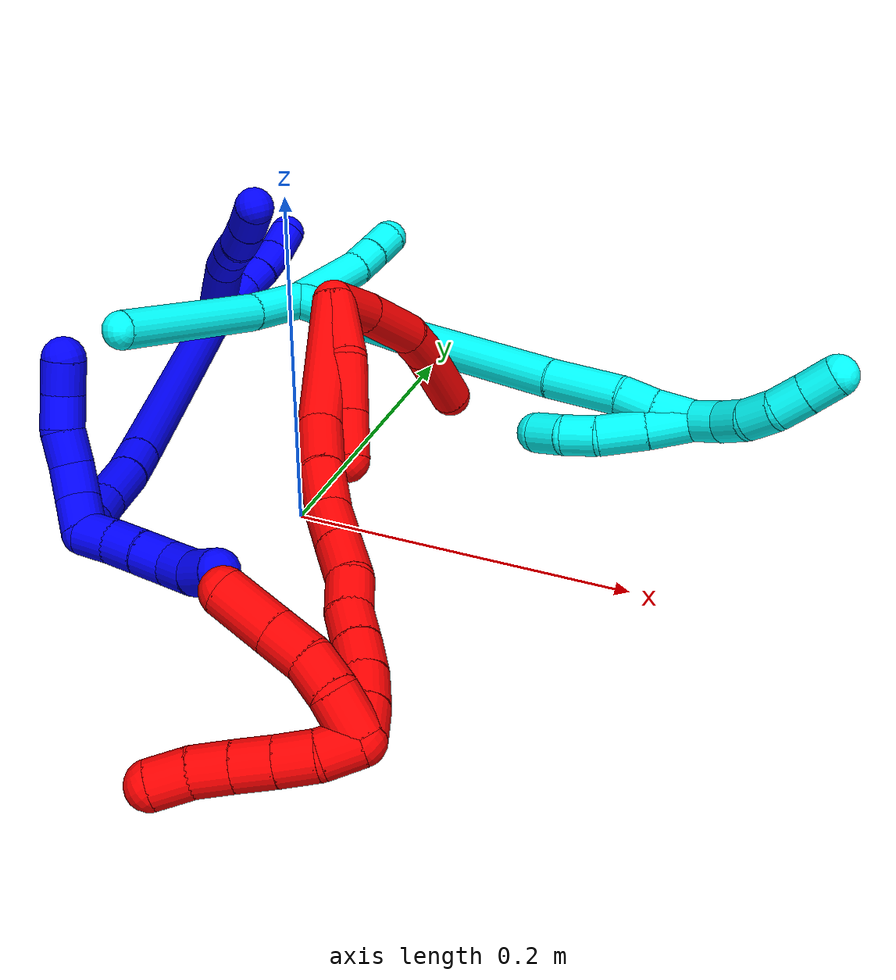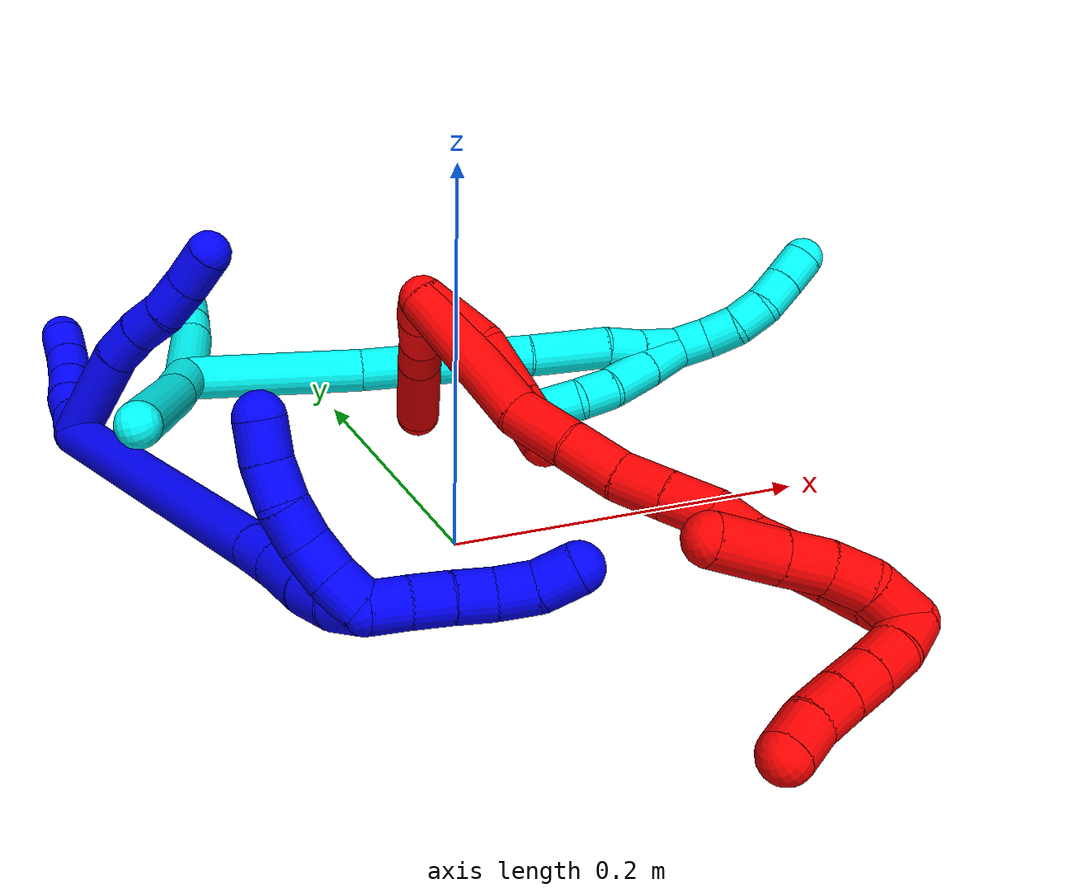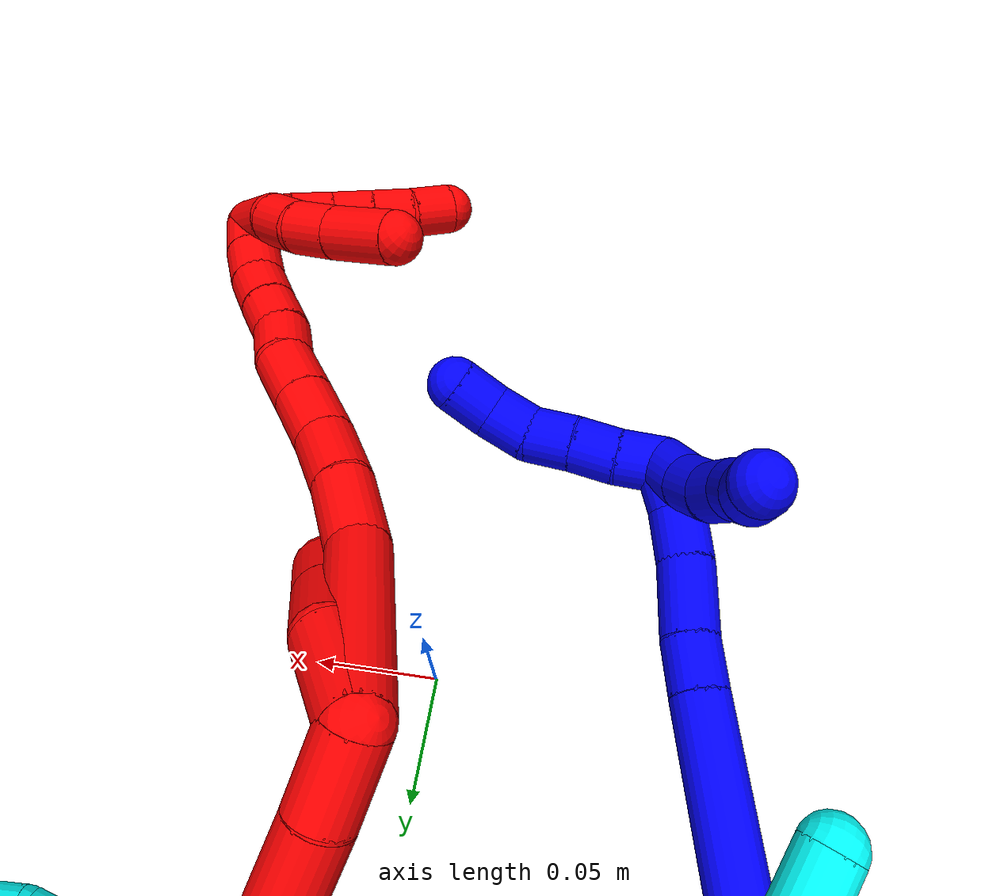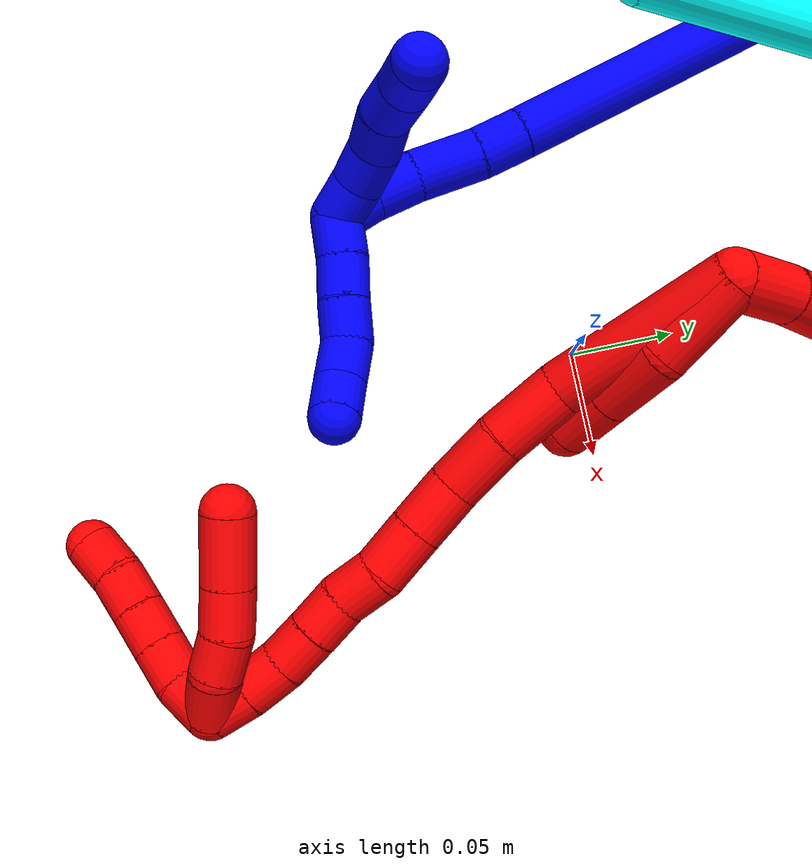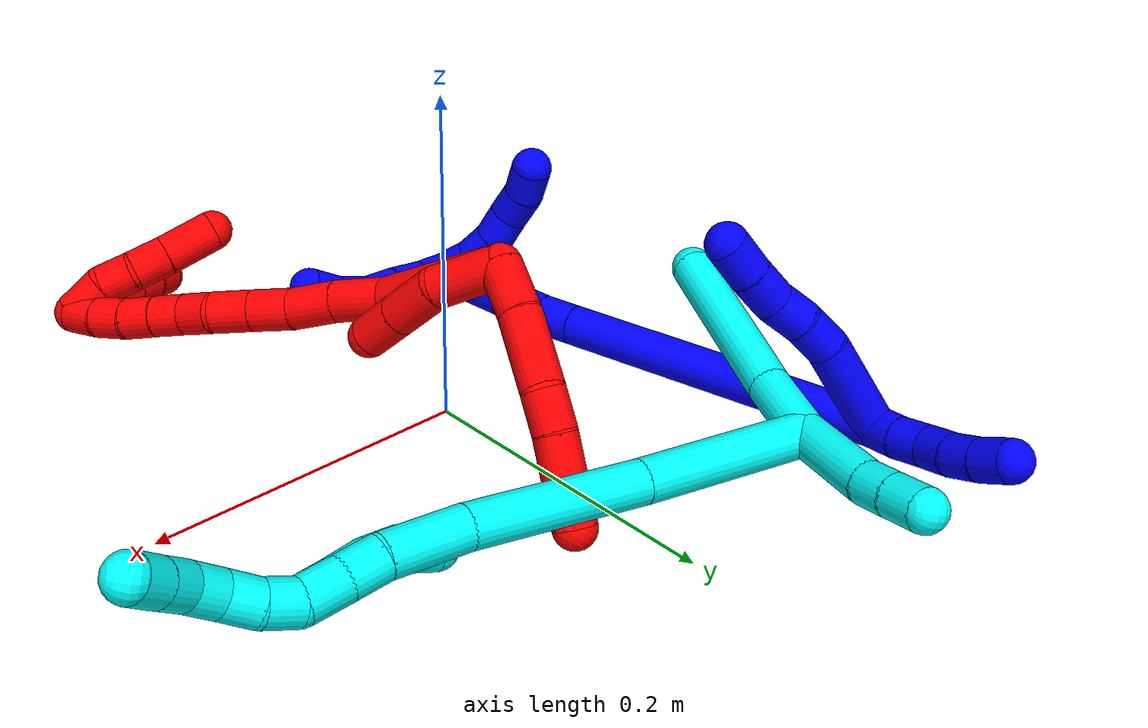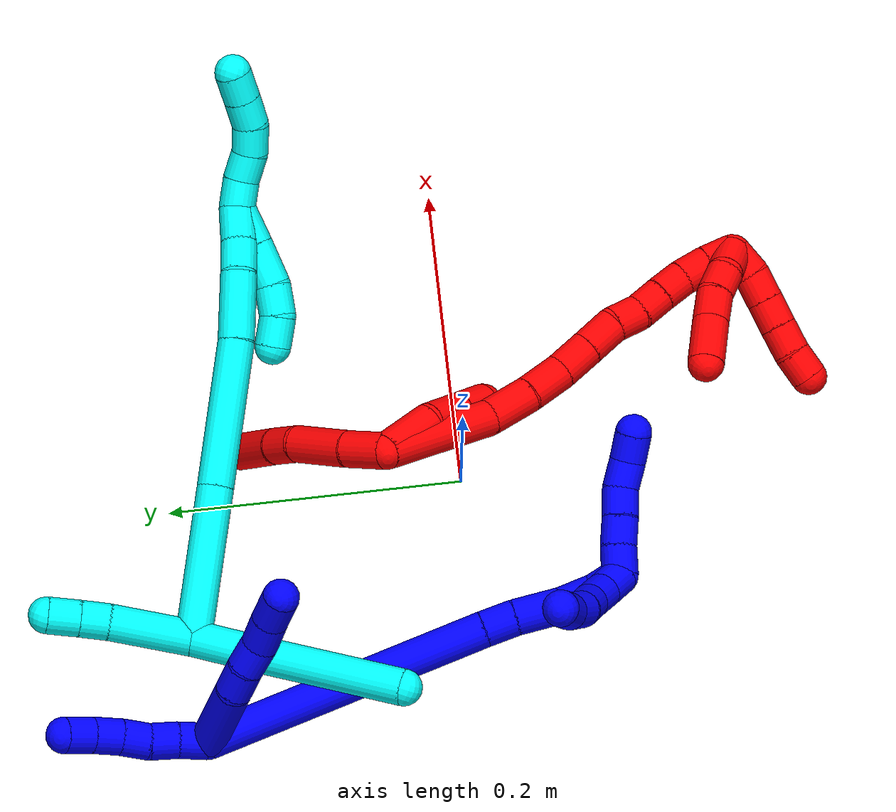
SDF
<sdf version="1.7">
 <world name="default">
  <plugin name="TubeGeneratorPlugin" filename="libtube_generator_plugin.so"/>
  <model name="photoneo_s_sensor">
   <static>1</static>
   <pose>0 0 2 1.57079 1.57079 3.14159</pose>
   <link name="link">
    <inertial><mass>0.1</mass></inertial>
    <sensor name="sensor" type="depth">
     <update_rate>30</update_rate>
     <camera>
      <horizontal_fov>1.22</horizontal_fov>
      <image><width>1920</width><height>1200</height><format>B8G8R8</format></image>
      <clip><near>0.1</near><far>4</far></clip>
      <depth_camera><output>points</output></depth_camera>
     </camera>
     <plugin name="camera_plugin" filename="libgazebo_ros_depth_camera.so">
      <baseline>0.2</baseline>
      <alwaysOn>1</alwaysOn>
      <updateRate>0.0</updateRate>
      <cameraName>camera_ir</cameraName>
      <imageTopicName>/camera/color/image_raw</imageTopicName>
      <cameraInfoTopicName>/camera/color/camera_info</cameraInfoTopicName>
      <depthImageTopicName>/camera/depth/image_raw</depthImageTopicName>
      <depthImageCameraInfoTopicName>/camera/depth/camera_info</depthImageCameraInfoTopicName>
      <pointCloudTopicName>/camera/depth/points</pointCloudTopicName>
      <frameName>fr_optical</frameName>
      <pointCloudCutoff>0.1</pointCloudCutoff>
      <pointCloudCutoffMax>2.0</pointCloudCutoffMax>
      <distortionK1>0</distortionK1>
      <distortionK2>0</distortionK2>
      <distortionK3>0</distortionK3>
      <distortionT1>0</distortionT1>
      <distortionT2>0</distortionT2>
      <CxPrime>0</CxPrime>
      <Cx>0</Cx>
      <Cy>0</Cy>
      <focalLength>0</focalLength>
      <hackBaseline>0</hackBaseline>
     </plugin>
    </sensor>
   </link>
  </model>
  <gravity>0 0 -9.8</gravity>
  <magnetic_field>6e-06 2.3e-05 -4.2e-05</magnetic_field>
  <atmosphere type="adiabatic"/>
  <physics name="default_physics" default="0" type="ode">
   <max_step_size>0.003</max_step_size>
   <real_time_factor>1</real_time_factor>
   <real_time_update_rate>1000</real_time_update_rate>
   <max_contacts>10000</max_contacts>
   <ode>
    <solver>
     <type>quick</type>
     <iters>100</iters>
     <sor>1.3</sor>
     <use_dynamic_moi_rescaling>0</use_dynamic_moi_rescaling>
    </solver>
    <constraints>
     <contact_max_correcting_vel>0</contact_max_correcting_vel>
     <contact_surface_layer>0.001</contact_surface_layer>
     <cfm>0</cfm>
     <erp>0.2</erp>
    </constraints>
   </ode>
  </physics>
  <scene><ambient>0.4 0.4 0.4 1</ambient><background>0.7 0.7 0.7 1</background><shadows>0</shadows></scene>
  <audio><device>default</device></audio>
  <spherical_coordinates>
   <surface_model>EARTH_WGS84</surface_model>
   <latitude_deg>0</latitude_deg>
   <longitude_deg>0</longitude_deg>
   <elevation>0</elevation>
   <heading_deg>0</heading_deg>
  </spherical_coordinates>
  <model name="bin">
   <static>1</static>
   <link name="bottom">
    <collision name="collision-bottom">
     <pose>0 0 -0.01 0 -0 0</pose>
     <geometry><box><size>0.8 0.6 0.02</size></box></geometry>
     <surface>
      <friction><ode><mu>100</mu><mu2>100</mu2></ode></friction>
      <contact><collide_bitmask>65535</collide_bitmask></contact>
     </surface>
    </collision>
   </link>
   <link name="west_wall">
    <collision name="collision-west_wall">
     <pose>-0.41 0 0.1 0 -0 0</pose>
     <geometry><box><size>0.02 0.6 0.2</size></box></geometry>
     <surface>
      <friction><ode><mu>100</mu><mu2>100</mu2></ode></friction>
      <contact><collide_bitmask>65535</collide_bitmask></contact>
     </surface>
    </collision>
   </link>
   <link name="east_wall">
    <collision name="collision-east_wall">
     <pose>0.41 0 0.1 0 -0 0</pose>
     <geometry><box><size>0.02 0.6 0.2</size></box></geometry>
     <surface>
      <friction><ode><mu>100</mu><mu2>100</mu2></ode></friction>
      <contact><collide_bitmask>65535</collide_bitmask></contact>
     </surface>
    </collision>
   </link>
   <link name="south_wall">
    <collision name="collision-south_wall">
     <pose>0 -0.31 0.1 0 -0 0</pose>
     <geometry><box><size>0.8 0.02 0.2</size></box></geometry>
     <surface>
      <friction><ode><mu>100</mu><mu2>100</mu2></ode></friction>
      <contact><collide_bitmask>65535</collide_bitmask></contact>
     </surface>
    </collision>
   </link>
   <link name="north_wall">
    <collision name="collision-north_wall">
     <pose>0 0.31 0.1 0 -0 0</pose>
     <geometry><box><size>0.8 0.02 0.2</size></box></geometry>
     <surface>
      <friction><ode><mu>100</mu><mu2>100</mu2></ode></friction>
      <contact><collide_bitmask>65535</collide_bitmask></contact>
     </surface>
    </collision>
   </link>
  </model>
  <model name="1">
   <static>0</static>
   <link name="1">
    <collision name="collision-cylinder-e_1_2_8">
     <pose>0.017997 -0.017629 0.016981 0.804104 0.63399 0.277201</pose>
     <geometry><cylinder><radius>0.0125</radius><length>0.060762</length></cylinder></geometry>
     <surface>
      <friction><ode><mu>1.16</mu><mu2>1.16</mu2><slip1>0</slip1><slip2>0</slip2></ode></friction>
      <contact><ode><kp>1e+06</kp><kd>1</kd><max_vel>0</max_vel><min_depth>0.001</min_depth></ode></contact>
     </surface>
    </collision>
    <visual name="visual-cylinder-e_1_2_8">
     <pose>0.017997 -0.017629 0.016981 0.804104 0.63399 0.277201</pose>
     <geometry><cylinder><radius>0.0125</radius><length>0.060762</length></cylinder></geometry>
     <material><ambient>0 0 1 1</ambient></material>
    </visual>
    <collision name="collision-cylinder-e_2_8_9">
     <pose>0.043613 -0.042377 0.038052 1.04939 0.748079 0.446804</pose>
     <geometry><cylinder><radius>0.0125</radius><length>0.022403</length></cylinder></geometry>
     <surface>
      <friction><ode><mu>1.16</mu><mu2>1.16</mu2><slip1>0</slip1><slip2>0</slip2></ode></friction>
      <contact><ode><kp>1e+06</kp><kd>1</kd><max_vel>0</max_vel><min_depth>0.001</min_depth></ode></contact>
     </surface>
    </collision>
    <visual name="visual-cylinder-e_2_8_9">
     <pose>0.043613 -0.042377 0.038052 1.04939 0.748079 0.446804</pose>
     <geometry><cylinder><radius>0.0125</radius><length>0.022403</length></cylinder></geometry>
     <material><ambient>0 0 1 1</ambient></material>
    </visual>
    <collision name="collision-cylinder-e_3_9_10">
     <pose>0.058343 -0.056909 0.044534 1.25863 0.73992 0.550387</pose>
     <geometry><cylinder><radius>0.0125</radius><length>0.021094</length></cylinder></geometry>
     <surface>
      <friction><ode><mu>1.16</mu><mu2>1.16</mu2><slip1>0</slip1><slip2>0</slip2></ode></friction>
      <contact><ode><kp>1e+06</kp><kd>1</kd><max_vel>0</max_vel><min_depth>0.001</min_depth></ode></contact>
     </surface>
    </collision>
    <visual name="visual-cylinder-e_3_9_10">
     <pose>0.058343 -0.056909 0.044534 1.25863 0.73992 0.550387</pose>
     <geometry><cylinder><radius>0.0125</radius><length>0.021094</length></cylinder></geometry>
     <material><ambient>0 0 1 1</ambient></material>
    </visual>
    <collision name="collision-cylinder-e_4_10_11">
     <pose>0.07337 -0.071004 0.051713 0.949192 0.766576 0.408549</pose>
     <geometry><cylinder><radius>0.0125</radius><length>0.022823</length></cylinder></geometry>
     <surface>
      <friction><ode><mu>1.16</mu><mu2>1.16</mu2><slip1>0</slip1><slip2>0</slip2></ode></friction>
      <contact><ode><kp>1e+06</kp><kd>1</kd><max_vel>0</max_vel><min_depth>0.001</min_depth></ode></contact>
     </surface>
    </collision>
    <visual name="visual-cylinder-e_4_10_11">
     <pose>0.07337 -0.071004 0.051713 0.949192 0.766576 0.408549</pose>
     <geometry><cylinder><radius>0.0125</radius><length>0.022823</length></cylinder></geometry>
     <material><ambient>0 0 1 1</ambient></material>
    </visual>
    <collision name="collision-cylinder-e_5_11_6">
     <pose>0.088642 -0.084578 0.061948 0.901842 0.697062 0.348311</pose>
     <geometry><cylinder><radius>0.0125</radius><length>0.022919</length></cylinder></geometry>
     <surface>
      <friction><ode><mu>1.16</mu><mu2>1.16</mu2><slip1>0</slip1><slip2>0</slip2></ode></friction>
      <contact><ode><kp>1e+06</kp><kd>1</kd><max_vel>0</max_vel><min_depth>0.001</min_depth></ode></contact>
     </surface>
    </collision>
    <visual name="visual-cylinder-e_5_11_6">
     <pose>0.088642 -0.084578 0.061948 0.901842 0.697062 0.348311</pose>
     <geometry><cylinder><radius>0.0125</radius><length>0.022919</length></cylinder></geometry>
     <material><ambient>0 0 1 1</ambient></material>
    </visual>
    <collision name="collision-cylinder-e_1_2_12">
     <pose>0.0031 0.009049 0.002917 -1.2589 0.315237 -0.230474</pose>
     <geometry><cylinder><radius>0.0125</radius><length>0.02</length></cylinder></geometry>
     <surface>
      <friction><ode><mu>1.16</mu><mu2>1.16</mu2><slip1>0</slip1><slip2>0</slip2></ode></friction>
      <contact><ode><kp>1e+06</kp><kd>1</kd><max_vel>0</max_vel><min_depth>0.001</min_depth></ode></contact>
     </surface>
    </collision>
    <visual name="visual-cylinder-e_1_2_12">
     <pose>0.0031 0.009049 0.002917 -1.2589 0.315237 -0.230474</pose>
     <geometry><cylinder><radius>0.0125</radius><length>0.02</length></cylinder></geometry>
     <material><ambient>0 0 1 1</ambient></material>
    </visual>
    <collision name="collision-cylinder-e_2_12_13">
     <pose>0.008414 0.02709 0.009607 -1.17368 0.22312 -0.148716</pose>
     <geometry><cylinder><radius>0.0125</radius><length>0.02</length></cylinder></geometry>
     <surface>
      <friction><ode><mu>1.16</mu><mu2>1.16</mu2><slip1>0</slip1><slip2>0</slip2></ode></friction>
      <contact><ode><kp>1e+06</kp><kd>1</kd><max_vel>0</max_vel><min_depth>0.001</min_depth></ode></contact>
     </surface>
    </collision>
    <visual name="visual-cylinder-e_2_12_13">
     <pose>0.008414 0.02709 0.009607 -1.17368 0.22312 -0.148716</pose>
     <geometry><cylinder><radius>0.0125</radius><length>0.02</length></cylinder></geometry>
     <material><ambient>0 0 1 1</ambient></material>
    </visual>
    <collision name="collision-cylinder-e_3_13_14">
     <pose>0.014975 0.04424 0.017193 -1.13335 0.449938 -0.289186</pose>
     <geometry><cylinder><radius>0.0125</radius><length>0.02</length></cylinder></geometry>
     <surface>
      <friction><ode><mu>1.16</mu><mu2>1.16</mu2><slip1>0</slip1><slip2>0</slip2></ode></friction>
      <contact><ode><kp>1e+06</kp><kd>1</kd><max_vel>0</max_vel><min_depth>0.001</min_depth></ode></contact>
     </surface>
    </collision>
    <visual name="visual-cylinder-e_3_13_14">
     <pose>0.014975 0.04424 0.017193 -1.13335 0.449938 -0.289186</pose>
     <geometry><cylinder><radius>0.0125</radius><length>0.02</length></cylinder></geometry>
     <material><ambient>0 0 1 1</ambient></material>
    </visual>
    <collision name="collision-cylinder-e_4_14_15">
     <pose>0.022846 0.060408 0.025847 -1.02732 0.359911 -0.204557</pose>
     <geometry><cylinder><radius>0.0125</radius><length>0.02</length></cylinder></geometry>
     <surface>
      <friction><ode><mu>1.16</mu><mu2>1.16</mu2><slip1>0</slip1><slip2>0</slip2></ode></friction>
      <contact><ode><kp>1e+06</kp><kd>1</kd><max_vel>0</max_vel><min_depth>0.001</min_depth></ode></contact>
     </surface>
    </collision>
    <visual name="visual-cylinder-e_4_14_15">
     <pose>0.022846 0.060408 0.025847 -1.02732 0.359911 -0.204557</pose>
     <geometry><cylinder><radius>0.0125</radius><length>0.02</length></cylinder></geometry>
     <material><ambient>0 0 1 1</ambient></material>
    </visual>
    <collision name="collision-cylinder-e_5_15_5">
     <pose>0.029364 0.076044 0.036421 -0.926027 0.304255 -0.152771</pose>
     <geometry><cylinder><radius>0.0125</radius><length>0.02</length></cylinder></geometry>
     <surface>
      <friction><ode><mu>1.16</mu><mu2>1.16</mu2><slip1>0</slip1><slip2>0</slip2></ode></friction>
      <contact><ode><kp>1e+06</kp><kd>1</kd><max_vel>0</max_vel><min_depth>0.001</min_depth></ode></contact>
     </surface>
    </collision>
    <visual name="visual-cylinder-e_5_15_5">
     <pose>0.029364 0.076044 0.036421 -0.926027 0.304255 -0.152771</pose>
     <geometry><cylinder><radius>0.0125</radius><length>0.02</length></cylinder></geometry>
     <material><ambient>0 0 1 1</ambient></material>
    </visual>
    <collision name="collision-cylinder-e_1_2_16">
     <pose>0.012491 -0.095284 -0.028456 1.86101 0.124952 0.167547</pose>
     <geometry><cylinder><radius>0.0125</radius><length>0.200448</length></cylinder></geometry>
     <surface>
      <friction><ode><mu>1.16</mu><mu2>1.16</mu2><slip1>0</slip1><slip2>0</slip2></ode></friction>
      <contact><ode><kp>1e+06</kp><kd>1</kd><max_vel>0</max_vel><min_depth>0.001</min_depth></ode></contact>
     </surface>
    </collision>
    <visual name="visual-cylinder-e_1_2_16">
     <pose>0.012491 -0.095284 -0.028456 1.86101 0.124952 0.167547</pose>
     <geometry><cylinder><radius>0.0125</radius><length>0.200448</length></cylinder></geometry>
     <material><ambient>0 0 1 1</ambient></material>
    </visual>
    <collision name="collision-cylinder-e_2_16_17">
     <pose>0.026064 -0.201428 -0.060245 1.86855 0.09503 0.128486</pose>
     <geometry><cylinder><radius>0.0125</radius><length>0.022822</length></cylinder></geometry>
     <surface>
      <friction><ode><mu>1.16</mu><mu2>1.16</mu2><slip1>0</slip1><slip2>0</slip2></ode></friction>
      <contact><ode><kp>1e+06</kp><kd>1</kd><max_vel>0</max_vel><min_depth>0.001</min_depth></ode></contact>
     </surface>
    </collision>
    <visual name="visual-cylinder-e_2_16_17">
     <pose>0.026064 -0.201428 -0.060245 1.86855 0.09503 0.128486</pose>
     <geometry><cylinder><radius>0.0125</radius><length>0.022822</length></cylinder></geometry>
     <material><ambient>0 0 1 1</ambient></material>
    </visual>
    <collision name="collision-cylinder-e_3_17_18">
     <pose>0.027195 -0.228196 -0.067499 1.81245 0.002937 0.003749</pose>
     <geometry><cylinder><radius>0.0125</radius><length>0.032768</length></cylinder></geometry>
     <surface>
      <friction><ode><mu>1.16</mu><mu2>1.16</mu2><slip1>0</slip1><slip2>0</slip2></ode></friction>
      <contact><ode><kp>1e+06</kp><kd>1</kd><max_vel>0</max_vel><min_depth>0.001</min_depth></ode></contact>
     </surface>
    </collision>
    <visual name="visual-cylinder-e_3_17_18">
     <pose>0.027195 -0.228196 -0.067499 1.81245 0.002937 0.003749</pose>
     <geometry><cylinder><radius>0.0125</radius><length>0.032768</length></cylinder></geometry>
     <material><ambient>0 0 1 1</ambient></material>
    </visual>
    <collision name="collision-cylinder-e_4_18_19">
     <pose>0.028911 -0.255638 -0.073784 1.77298 0.140699 0.172323</pose>
     <geometry><cylinder><radius>0.0125</radius><length>0.023782</length></cylinder></geometry>
     <surface>
      <friction><ode><mu>1.16</mu><mu2>1.16</mu2><slip1>0</slip1><slip2>0</slip2></ode></friction>
      <contact><ode><kp>1e+06</kp><kd>1</kd><max_vel>0</max_vel><min_depth>0.001</min_depth></ode></contact>
     </surface>
    </collision>
    <visual name="visual-cylinder-e_4_18_19">
     <pose>0.028911 -0.255638 -0.073784 1.77298 0.140699 0.172323</pose>
     <geometry><cylinder><radius>0.0125</radius><length>0.023782</length></cylinder></geometry>
     <material><ambient>0 0 1 1</ambient></material>
    </visual>
    <collision name="collision-cylinder-e_5_19_1">
     <pose>0.033953 -0.276631 -0.077111 1.67219 0.341046 0.37669</pose>
     <geometry><cylinder><radius>0.0125</radius><length>0.020179</length></cylinder></geometry>
     <surface>
      <friction><ode><mu>1.16</mu><mu2>1.16</mu2><slip1>0</slip1><slip2>0</slip2></ode></friction>
      <contact><ode><kp>1e+06</kp><kd>1</kd><max_vel>0</max_vel><min_depth>0.001</min_depth></ode></contact>
     </surface>
    </collision>
    <visual name="visual-cylinder-e_5_19_1">
     <pose>0.033953 -0.276631 -0.077111 1.67219 0.341046 0.37669</pose>
     <geometry><cylinder><radius>0.0125</radius><length>0.020179</length></cylinder></geometry>
     <material><ambient>0 0 1 1</ambient></material>
    </visual>
    <collision name="collision-cylinder-e_1_1_20">
     <pose>0.035098 -0.281021 -0.069747 -0.5469 -0.224838 0.063307</pose>
     <geometry><cylinder><radius>0.0125</radius><length>0.02</length></cylinder></geometry>
     <surface>
      <friction><ode><mu>1.16</mu><mu2>1.16</mu2><slip1>0</slip1><slip2>0</slip2></ode></friction>
      <contact><ode><kp>1e+06</kp><kd>1</kd><max_vel>0</max_vel><min_depth>0.001</min_depth></ode></contact>
     </surface>
    </collision>
    <visual name="visual-cylinder-e_1_1_20">
     <pose>0.035098 -0.281021 -0.069747 -0.5469 -0.224838 0.063307</pose>
     <geometry><cylinder><radius>0.0125</radius><length>0.02</length></cylinder></geometry>
     <material><ambient>0 0 1 1</ambient></material>
    </visual>
    <collision name="collision-cylinder-e_2_20_21">
     <pose>0.031755 -0.272476 -0.05211 -0.357264 -0.111613 0.020173</pose>
     <geometry><cylinder><radius>0.0125</radius><length>0.02</length></cylinder></geometry>
     <surface>
      <friction><ode><mu>1.16</mu><mu2>1.16</mu2><slip1>0</slip1><slip2>0</slip2></ode></friction>
      <contact><ode><kp>1e+06</kp><kd>1</kd><max_vel>0</max_vel><min_depth>0.001</min_depth></ode></contact>
     </surface>
    </collision>
    <visual name="visual-cylinder-e_2_20_21">
     <pose>0.031755 -0.272476 -0.05211 -0.357264 -0.111613 0.020173</pose>
     <geometry><cylinder><radius>0.0125</radius><length>0.02</length></cylinder></geometry>
     <material><ambient>0 0 1 1</ambient></material>
    </visual>
    <collision name="collision-cylinder-e_3_21_22">
     <pose>0.030421 -0.267923 -0.03286 -0.108042 -0.022044 0.001192</pose>
     <geometry><cylinder><radius>0.0125</radius><length>0.02</length></cylinder></geometry>
     <surface>
      <friction><ode><mu>1.16</mu><mu2>1.16</mu2><slip1>0</slip1><slip2>0</slip2></ode></friction>
      <contact><ode><kp>1e+06</kp><kd>1</kd><max_vel>0</max_vel><min_depth>0.001</min_depth></ode></contact>
     </surface>
    </collision>
    <visual name="visual-cylinder-e_3_21_22">
     <pose>0.030421 -0.267923 -0.03286 -0.108042 -0.022044 0.001192</pose>
     <geometry><cylinder><radius>0.0125</radius><length>0.02</length></cylinder></geometry>
     <material><ambient>0 0 1 1</ambient></material>
    </visual>
    <collision name="collision-cylinder-e_4_22_23">
     <pose>0.032028 -0.264291 -0.013427 -0.262784 0.183803 -0.024358</pose>
     <geometry><cylinder><radius>0.0125</radius><length>0.02</length></cylinder></geometry>
     <surface>
      <friction><ode><mu>1.16</mu><mu2>1.16</mu2><slip1>0</slip1><slip2>0</slip2></ode></friction>
      <contact><ode><kp>1e+06</kp><kd>1</kd><max_vel>0</max_vel><min_depth>0.001</min_depth></ode></contact>
     </surface>
    </collision>
    <visual name="visual-cylinder-e_4_22_23">
     <pose>0.032028 -0.264291 -0.013427 -0.262784 0.183803 -0.024358</pose>
     <geometry><cylinder><radius>0.0125</radius><length>0.02</length></cylinder></geometry>
     <material><ambient>0 0 1 1</ambient></material>
    </visual>
    <collision name="collision-cylinder-e_5_23_4">
     <pose>0.03708 -0.261229 0.005519 -0.053728 0.328268 -0.008901</pose>
     <geometry><cylinder><radius>0.0125</radius><length>0.02</length></cylinder></geometry>
     <surface>
      <friction><ode><mu>1.16</mu><mu2>1.16</mu2><slip1>0</slip1><slip2>0</slip2></ode></friction>
      <contact><ode><kp>1e+06</kp><kd>1</kd><max_vel>0</max_vel><min_depth>0.001</min_depth></ode></contact>
     </surface>
    </collision>
    <visual name="visual-cylinder-e_5_23_4">
     <pose>0.03708 -0.261229 0.005519 -0.053728 0.328268 -0.008901</pose>
     <geometry><cylinder><radius>0.0125</radius><length>0.02</length></cylinder></geometry>
     <material><ambient>0 0 1 1</ambient></material>
    </visual>
    <collision name="collision-cylinder-e_1_1_24">
     <pose>0.04647 -0.287212 -0.081967 2.86132 1.15363 2.71458</pose>
     <geometry><cylinder><radius>0.0125</radius><length>0.02</length></cylinder></geometry>
     <surface>
      <friction><ode><mu>1.16</mu><mu2>1.16</mu2><slip1>0</slip1><slip2>0</slip2></ode></friction>
      <contact><ode><kp>1e+06</kp><kd>1</kd><max_vel>0</max_vel><min_depth>0.001</min_depth></ode></contact>
     </surface>
    </collision>
    <visual name="visual-cylinder-e_1_1_24">
     <pose>0.04647 -0.287212 -0.081967 2.86132 1.15363 2.71458</pose>
     <geometry><cylinder><radius>0.0125</radius><length>0.02</length></cylinder></geometry>
     <material><ambient>0 0 1 1</ambient></material>
    </visual>
    <collision name="collision-cylinder-e_2_24_25">
     <pose>0.064587 -0.290638 -0.089621 2.59166 1.11395 2.29088</pose>
     <geometry><cylinder><radius>0.0125</radius><length>0.02</length></cylinder></geometry>
     <surface>
      <friction><ode><mu>1.16</mu><mu2>1.16</mu2><slip1>0</slip1><slip2>0</slip2></ode></friction>
      <contact><ode><kp>1e+06</kp><kd>1</kd><max_vel>0</max_vel><min_depth>0.001</min_depth></ode></contact>
     </surface>
    </collision>
    <visual name="visual-cylinder-e_2_24_25">
     <pose>0.064587 -0.290638 -0.089621 2.59166 1.11395 2.29088</pose>
     <geometry><cylinder><radius>0.0125</radius><length>0.02</length></cylinder></geometry>
     <material><ambient>0 0 1 1</ambient></material>
    </visual>
    <collision name="collision-cylinder-e_3_25_26">
     <pose>0.08247 -0.294583 -0.097619 2.77229 1.09921 2.54967</pose>
     <geometry><cylinder><radius>0.0125</radius><length>0.02</length></cylinder></geometry>
     <surface>
      <friction><ode><mu>1.16</mu><mu2>1.16</mu2><slip1>0</slip1><slip2>0</slip2></ode></friction>
      <contact><ode><kp>1e+06</kp><kd>1</kd><max_vel>0</max_vel><min_depth>0.001</min_depth></ode></contact>
     </surface>
    </collision>
    <visual name="visual-cylinder-e_3_25_26">
     <pose>0.08247 -0.294583 -0.097619 2.77229 1.09921 2.54967</pose>
     <geometry><cylinder><radius>0.0125</radius><length>0.02</length></cylinder></geometry>
     <material><ambient>0 0 1 1</ambient></material>
    </visual>
    <collision name="collision-cylinder-e_4_26_27">
     <pose>0.10003 -0.300634 -0.104242 2.06675 1.04547 1.53713</pose>
     <geometry><cylinder><radius>0.0125</radius><length>0.02</length></cylinder></geometry>
     <surface>
      <friction><ode><mu>1.16</mu><mu2>1.16</mu2><slip1>0</slip1><slip2>0</slip2></ode></friction>
      <contact><ode><kp>1e+06</kp><kd>1</kd><max_vel>0</max_vel><min_depth>0.001</min_depth></ode></contact>
     </surface>
    </collision>
    <visual name="visual-cylinder-e_4_26_27">
     <pose>0.10003 -0.300634 -0.104242 2.06675 1.04547 1.53713</pose>
     <geometry><cylinder><radius>0.0125</radius><length>0.02</length></cylinder></geometry>
     <material><ambient>0 0 1 1</ambient></material>
    </visual>
    <collision name="collision-cylinder-e_5_27_3">
     <pose>0.117658 -0.309426 -0.106162 1.46478 1.11453 1.02151</pose>
     <geometry><cylinder><radius>0.0125</radius><length>0.02</length></cylinder></geometry>
     <surface>
      <friction><ode><mu>1.16</mu><mu2>1.16</mu2><slip1>0</slip1><slip2>0</slip2></ode></friction>
      <contact><ode><kp>1e+06</kp><kd>1</kd><max_vel>0</max_vel><min_depth>0.001</min_depth></ode></contact>
     </surface>
    </collision>
    <visual name="visual-cylinder-e_5_27_3">
     <pose>0.117658 -0.309426 -0.106162 1.46478 1.11453 1.02151</pose>
     <geometry><cylinder><radius>0.0125</radius><length>0.02</length></cylinder></geometry>
     <material><ambient>0 0 1 1</ambient></material>
    </visual>
    <collision name="collision-sphere-3">
     <pose>0.126635 -0.313807 -0.105696 0 -0 0</pose>
     <geometry><sphere><radius>0.0125</radius></sphere></geometry>
     <surface>
      <friction><ode><mu>1.16</mu><mu2>1.16</mu2><slip1>0</slip1><slip2>0</slip2></ode></friction>
      <contact><ode><kp>1e+06</kp><kd>1</kd><max_vel>0</max_vel><min_depth>0.001</min_depth></ode></contact>
     </surface>
    </collision>
    <visual name="visual-sphere-3">
     <pose>0.126635 -0.313807 -0.105696 0 -0 0</pose>
     <geometry><sphere><radius>0.0125</radius></sphere></geometry>
     <material><ambient>0 0 1 1</ambient></material>
    </visual>
    <collision name="collision-sphere-27">
     <pose>0.108681 -0.305044 -0.106629 0 -0 0</pose>
     <geometry><sphere><radius>0.0125</radius></sphere></geometry>
     <surface>
      <friction><ode><mu>1.16</mu><mu2>1.16</mu2><slip1>0</slip1><slip2>0</slip2></ode></friction>
      <contact><ode><kp>1e+06</kp><kd>1</kd><max_vel>0</max_vel><min_depth>0.001</min_depth></ode></contact>
     </surface>
    </collision>
    <visual name="visual-sphere-27">
     <pose>0.108681 -0.305044 -0.106629 0 -0 0</pose>
     <geometry><sphere><radius>0.0125</radius></sphere></geometry>
     <material><ambient>0 0 1 1</ambient></material>
    </visual>
    <collision name="collision-sphere-26">
     <pose>0.091378 -0.296223 -0.101856 0 -0 0</pose>
     <geometry><sphere><radius>0.0125</radius></sphere></geometry>
     <surface>
      <friction><ode><mu>1.16</mu><mu2>1.16</mu2><slip1>0</slip1><slip2>0</slip2></ode></friction>
      <contact><ode><kp>1e+06</kp><kd>1</kd><max_vel>0</max_vel><min_depth>0.001</min_depth></ode></contact>
     </surface>
    </collision>
    <visual name="visual-sphere-26">
     <pose>0.091378 -0.296223 -0.101856 0 -0 0</pose>
     <geometry><sphere><radius>0.0125</radius></sphere></geometry>
     <material><ambient>0 0 1 1</ambient></material>
    </visual>
    <collision name="collision-sphere-25">
     <pose>0.073561 -0.292943 -0.093382 0 -0 0</pose>
     <geometry><sphere><radius>0.0125</radius></sphere></geometry>
     <surface>
      <friction><ode><mu>1.16</mu><mu2>1.16</mu2><slip1>0</slip1><slip2>0</slip2></ode></friction>
      <contact><ode><kp>1e+06</kp><kd>1</kd><max_vel>0</max_vel><min_depth>0.001</min_depth></ode></contact>
     </surface>
    </collision>
    <visual name="visual-sphere-25">
     <pose>0.073561 -0.292943 -0.093382 0 -0 0</pose>
     <geometry><sphere><radius>0.0125</radius></sphere></geometry>
     <material><ambient>0 0 1 1</ambient></material>
    </visual>
    <collision name="collision-sphere-24">
     <pose>0.055612 -0.288332 -0.08586 0 -0 0</pose>
     <geometry><sphere><radius>0.0125</radius></sphere></geometry>
     <surface>
      <friction><ode><mu>1.16</mu><mu2>1.16</mu2><slip1>0</slip1><slip2>0</slip2></ode></friction>
      <contact><ode><kp>1e+06</kp><kd>1</kd><max_vel>0</max_vel><min_depth>0.001</min_depth></ode></contact>
     </surface>
    </collision>
    <visual name="visual-sphere-24">
     <pose>0.055612 -0.288332 -0.08586 0 -0 0</pose>
     <geometry><sphere><radius>0.0125</radius></sphere></geometry>
     <material><ambient>0 0 1 1</ambient></material>
    </visual>
    <collision name="collision-sphere-4">
     <pose>0.040304 -0.26072 0.014972 0 -0 0</pose>
     <geometry><sphere><radius>0.0125</radius></sphere></geometry>
     <surface>
      <friction><ode><mu>1.16</mu><mu2>1.16</mu2><slip1>0</slip1><slip2>0</slip2></ode></friction>
      <contact><ode><kp>1e+06</kp><kd>1</kd><max_vel>0</max_vel><min_depth>0.001</min_depth></ode></contact>
     </surface>
    </collision>
    <visual name="visual-sphere-4">
     <pose>0.040304 -0.26072 0.014972 0 -0 0</pose>
     <geometry><sphere><radius>0.0125</radius></sphere></geometry>
     <material><ambient>0 0 1 1</ambient></material>
    </visual>
    <collision name="collision-sphere-23">
     <pose>0.033856 -0.261737 -0.003933 0 -0 0</pose>
     <geometry><sphere><radius>0.0125</radius></sphere></geometry>
     <surface>
      <friction><ode><mu>1.16</mu><mu2>1.16</mu2><slip1>0</slip1><slip2>0</slip2></ode></friction>
      <contact><ode><kp>1e+06</kp><kd>1</kd><max_vel>0</max_vel><min_depth>0.001</min_depth></ode></contact>
     </surface>
    </collision>
    <visual name="visual-sphere-23">
     <pose>0.033856 -0.261737 -0.003933 0 -0 0</pose>
     <geometry><sphere><radius>0.0125</radius></sphere></geometry>
     <material><ambient>0 0 1 1</ambient></material>
    </visual>
    <collision name="collision-sphere-22">
     <pose>0.0302 -0.266845 -0.022921 0 -0 0</pose>
     <geometry><sphere><radius>0.0125</radius></sphere></geometry>
     <surface>
      <friction><ode><mu>1.16</mu><mu2>1.16</mu2><slip1>0</slip1><slip2>0</slip2></ode></friction>
      <contact><ode><kp>1e+06</kp><kd>1</kd><max_vel>0</max_vel><min_depth>0.001</min_depth></ode></contact>
     </surface>
    </collision>
    <visual name="visual-sphere-22">
     <pose>0.0302 -0.266845 -0.022921 0 -0 0</pose>
     <geometry><sphere><radius>0.0125</radius></sphere></geometry>
     <material><ambient>0 0 1 1</ambient></material>
    </visual>
    <collision name="collision-sphere-21">
     <pose>0.030641 -0.269001 -0.0428 0 -0 0</pose>
     <geometry><sphere><radius>0.0125</radius></sphere></geometry>
     <surface>
      <friction><ode><mu>1.16</mu><mu2>1.16</mu2><slip1>0</slip1><slip2>0</slip2></ode></friction>
      <contact><ode><kp>1e+06</kp><kd>1</kd><max_vel>0</max_vel><min_depth>0.001</min_depth></ode></contact>
     </surface>
    </collision>
    <visual name="visual-sphere-21">
     <pose>0.030641 -0.269001 -0.0428 0 -0 0</pose>
     <geometry><sphere><radius>0.0125</radius></sphere></geometry>
     <material><ambient>0 0 1 1</ambient></material>
    </visual>
    <collision name="collision-sphere-20">
     <pose>0.032869 -0.275952 -0.06142 0 -0 0</pose>
     <geometry><sphere><radius>0.0125</radius></sphere></geometry>
     <surface>
      <friction><ode><mu>1.16</mu><mu2>1.16</mu2><slip1>0</slip1><slip2>0</slip2></ode></friction>
      <contact><ode><kp>1e+06</kp><kd>1</kd><max_vel>0</max_vel><min_depth>0.001</min_depth></ode></contact>
     </surface>
    </collision>
    <visual name="visual-sphere-20">
     <pose>0.032869 -0.275952 -0.06142 0 -0 0</pose>
     <geometry><sphere><radius>0.0125</radius></sphere></geometry>
     <material><ambient>0 0 1 1</ambient></material>
    </visual>
    <collision name="collision-sphere-6">
     <pose>0.095999 -0.091471 0.067397 0 -0 0</pose>
     <geometry><sphere><radius>0.0125</radius></sphere></geometry>
     <surface>
      <friction><ode><mu>1.16</mu><mu2>1.16</mu2><slip1>0</slip1><slip2>0</slip2></ode></friction>
      <contact><ode><kp>1e+06</kp><kd>1</kd><max_vel>0</max_vel><min_depth>0.001</min_depth></ode></contact>
     </surface>
    </collision>
    <visual name="visual-sphere-6">
     <pose>0.095999 -0.091471 0.067397 0 -0 0</pose>
     <geometry><sphere><radius>0.0125</radius></sphere></geometry>
     <material><ambient>0 0 1 1</ambient></material>
    </visual>
    <collision name="collision-sphere-11">
     <pose>0.081286 -0.077686 0.056499 0 -0 0</pose>
     <geometry><sphere><radius>0.0125</radius></sphere></geometry>
     <surface>
      <friction><ode><mu>1.16</mu><mu2>1.16</mu2><slip1>0</slip1><slip2>0</slip2></ode></friction>
      <contact><ode><kp>1e+06</kp><kd>1</kd><max_vel>0</max_vel><min_depth>0.001</min_depth></ode></contact>
     </surface>
    </collision>
    <visual name="visual-sphere-11">
     <pose>0.081286 -0.077686 0.056499 0 -0 0</pose>
     <geometry><sphere><radius>0.0125</radius></sphere></geometry>
     <material><ambient>0 0 1 1</ambient></material>
    </visual>
    <collision name="collision-sphere-10">
     <pose>0.065454 -0.064322 0.046926 0 -0 0</pose>
     <geometry><sphere><radius>0.0125</radius></sphere></geometry>
     <surface>
      <friction><ode><mu>1.16</mu><mu2>1.16</mu2><slip1>0</slip1><slip2>0</slip2></ode></friction>
      <contact><ode><kp>1e+06</kp><kd>1</kd><max_vel>0</max_vel><min_depth>0.001</min_depth></ode></contact>
     </surface>
    </collision>
    <visual name="visual-sphere-10">
     <pose>0.065454 -0.064322 0.046926 0 -0 0</pose>
     <geometry><sphere><radius>0.0125</radius></sphere></geometry>
     <material><ambient>0 0 1 1</ambient></material>
    </visual>
    <collision name="collision-sphere-9">
     <pose>0.051232 -0.049496 0.042142 0 -0 0</pose>
     <geometry><sphere><radius>0.0125</radius></sphere></geometry>
     <surface>
      <friction><ode><mu>1.16</mu><mu2>1.16</mu2><slip1>0</slip1><slip2>0</slip2></ode></friction>
      <contact><ode><kp>1e+06</kp><kd>1</kd><max_vel>0</max_vel><min_depth>0.001</min_depth></ode></contact>
     </surface>
    </collision>
    <visual name="visual-sphere-9">
     <pose>0.051232 -0.049496 0.042142 0 -0 0</pose>
     <geometry><sphere><radius>0.0125</radius></sphere></geometry>
     <material><ambient>0 0 1 1</ambient></material>
    </visual>
    <collision name="collision-sphere-2">
     <geometry><sphere><radius>0.0125</radius></sphere></geometry>
     <surface>
      <friction><ode><mu>1.16</mu><mu2>1.16</mu2><slip1>0</slip1><slip2>0</slip2></ode></friction>
      <contact><ode><kp>1e+06</kp><kd>1</kd><max_vel>0</max_vel><min_depth>0.001</min_depth></ode></contact>
     </surface>
    </collision>
    <visual name="visual-sphere-2">
     <geometry><sphere><radius>0.0125</radius></sphere></geometry>
     <material><ambient>0 0 1 1</ambient></material>
    </visual>
    <collision name="collision-sphere-19">
     <pose>0.030578 -0.267172 -0.076148 0 -0 0</pose>
     <geometry><sphere><radius>0.0125</radius></sphere></geometry>
     <surface>
      <friction><ode><mu>1.16</mu><mu2>1.16</mu2><slip1>0</slip1><slip2>0</slip2></ode></friction>
      <contact><ode><kp>1e+06</kp><kd>1</kd><max_vel>0</max_vel><min_depth>0.001</min_depth></ode></contact>
     </surface>
    </collision>
    <visual name="visual-sphere-19">
     <pose>0.030578 -0.267172 -0.076148 0 -0 0</pose>
     <geometry><sphere><radius>0.0125</radius></sphere></geometry>
     <material><ambient>0 0 1 1</ambient></material>
    </visual>
    <collision name="collision-sphere-8">
     <pose>0.035993 -0.035257 0.033962 0 -0 0</pose>
     <geometry><sphere><radius>0.0125</radius></sphere></geometry>
     <surface>
      <friction><ode><mu>1.16</mu><mu2>1.16</mu2><slip1>0</slip1><slip2>0</slip2></ode></friction>
      <contact><ode><kp>1e+06</kp><kd>1</kd><max_vel>0</max_vel><min_depth>0.001</min_depth></ode></contact>
     </surface>
    </collision>
    <visual name="visual-sphere-8">
     <pose>0.035993 -0.035257 0.033962 0 -0 0</pose>
     <geometry><sphere><radius>0.0125</radius></sphere></geometry>
     <material><ambient>0 0 1 1</ambient></material>
    </visual>
    <collision name="collision-sphere-12">
     <pose>0.006201 0.018097 0.005835 0 -0 0</pose>
     <geometry><sphere><radius>0.0125</radius></sphere></geometry>
     <surface>
      <friction><ode><mu>1.16</mu><mu2>1.16</mu2><slip1>0</slip1><slip2>0</slip2></ode></friction>
      <contact><ode><kp>1e+06</kp><kd>1</kd><max_vel>0</max_vel><min_depth>0.001</min_depth></ode></contact>
     </surface>
    </collision>
    <visual name="visual-sphere-12">
     <pose>0.006201 0.018097 0.005835 0 -0 0</pose>
     <geometry><sphere><radius>0.0125</radius></sphere></geometry>
     <material><ambient>0 0 1 1</ambient></material>
    </visual>
    <collision name="collision-sphere-13">
     <pose>0.010626 0.036084 0.013378 0 -0 0</pose>
     <geometry><sphere><radius>0.0125</radius></sphere></geometry>
     <surface>
      <friction><ode><mu>1.16</mu><mu2>1.16</mu2><slip1>0</slip1><slip2>0</slip2></ode></friction>
      <contact><ode><kp>1e+06</kp><kd>1</kd><max_vel>0</max_vel><min_depth>0.001</min_depth></ode></contact>
     </surface>
    </collision>
    <visual name="visual-sphere-13">
     <pose>0.010626 0.036084 0.013378 0 -0 0</pose>
     <geometry><sphere><radius>0.0125</radius></sphere></geometry>
     <material><ambient>0 0 1 1</ambient></material>
    </visual>
    <collision name="collision-sphere-14">
     <pose>0.019324 0.052397 0.021008 0 -0 0</pose>
     <geometry><sphere><radius>0.0125</radius></sphere></geometry>
     <surface>
      <friction><ode><mu>1.16</mu><mu2>1.16</mu2><slip1>0</slip1><slip2>0</slip2></ode></friction>
      <contact><ode><kp>1e+06</kp><kd>1</kd><max_vel>0</max_vel><min_depth>0.001</min_depth></ode></contact>
     </surface>
    </collision>
    <visual name="visual-sphere-14">
     <pose>0.019324 0.052397 0.021008 0 -0 0</pose>
     <geometry><sphere><radius>0.0125</radius></sphere></geometry>
     <material><ambient>0 0 1 1</ambient></material>
    </visual>
    <collision name="collision-sphere-15">
     <pose>0.026368 0.068419 0.030687 0 -0 0</pose>
     <geometry><sphere><radius>0.0125</radius></sphere></geometry>
     <surface>
      <friction><ode><mu>1.16</mu><mu2>1.16</mu2><slip1>0</slip1><slip2>0</slip2></ode></friction>
      <contact><ode><kp>1e+06</kp><kd>1</kd><max_vel>0</max_vel><min_depth>0.001</min_depth></ode></contact>
     </surface>
    </collision>
    <visual name="visual-sphere-15">
     <pose>0.026368 0.068419 0.030687 0 -0 0</pose>
     <geometry><sphere><radius>0.0125</radius></sphere></geometry>
     <material><ambient>0 0 1 1</ambient></material>
    </visual>
    <collision name="collision-sphere-5">
     <pose>0.03236 0.083669 0.042155 0 -0 0</pose>
     <geometry><sphere><radius>0.0125</radius></sphere></geometry>
     <surface>
      <friction><ode><mu>1.16</mu><mu2>1.16</mu2><slip1>0</slip1><slip2>0</slip2></ode></friction>
      <contact><ode><kp>1e+06</kp><kd>1</kd><max_vel>0</max_vel><min_depth>0.001</min_depth></ode></contact>
     </surface>
    </collision>
    <visual name="visual-sphere-5">
     <pose>0.03236 0.083669 0.042155 0 -0 0</pose>
     <geometry><sphere><radius>0.0125</radius></sphere></geometry>
     <material><ambient>0 0 1 1</ambient></material>
    </visual>
    <collision name="collision-sphere-16">
     <pose>0.024981 -0.190569 -0.056913 0 -0 0</pose>
     <geometry><sphere><radius>0.0125</radius></sphere></geometry>
     <surface>
      <friction><ode><mu>1.16</mu><mu2>1.16</mu2><slip1>0</slip1><slip2>0</slip2></ode></friction>
      <contact><ode><kp>1e+06</kp><kd>1</kd><max_vel>0</max_vel><min_depth>0.001</min_depth></ode></contact>
     </surface>
    </collision>
    <visual name="visual-sphere-16">
     <pose>0.024981 -0.190569 -0.056913 0 -0 0</pose>
     <geometry><sphere><radius>0.0125</radius></sphere></geometry>
     <material><ambient>0 0 1 1</ambient></material>
    </visual>
    <collision name="collision-sphere-17">
     <pose>0.027147 -0.212288 -0.063578 0 -0 0</pose>
     <geometry><sphere><radius>0.0125</radius></sphere></geometry>
     <surface>
      <friction><ode><mu>1.16</mu><mu2>1.16</mu2><slip1>0</slip1><slip2>0</slip2></ode></friction>
      <contact><ode><kp>1e+06</kp><kd>1</kd><max_vel>0</max_vel><min_depth>0.001</min_depth></ode></contact>
     </surface>
    </collision>
    <visual name="visual-sphere-17">
     <pose>0.027147 -0.212288 -0.063578 0 -0 0</pose>
     <geometry><sphere><radius>0.0125</radius></sphere></geometry>
     <material><ambient>0 0 1 1</ambient></material>
    </visual>
    <collision name="collision-sphere-18">
     <pose>0.027243 -0.244104 -0.07142 0 -0 0</pose>
     <geometry><sphere><radius>0.0125</radius></sphere></geometry>
     <surface>
      <friction><ode><mu>1.16</mu><mu2>1.16</mu2><slip1>0</slip1><slip2>0</slip2></ode></friction>
      <contact><ode><kp>1e+06</kp><kd>1</kd><max_vel>0</max_vel><min_depth>0.001</min_depth></ode></contact>
     </surface>
    </collision>
    <visual name="visual-sphere-18">
     <pose>0.027243 -0.244104 -0.07142 0 -0 0</pose>
     <geometry><sphere><radius>0.0125</radius></sphere></geometry>
     <material><ambient>0 0 1 1</ambient></material>
    </visual>
    <collision name="collision-sphere-1">
     <pose>0.037328 -0.286091 -0.078073 0 -0 0</pose>
     <geometry><sphere><radius>0.0125</radius></sphere></geometry>
     <surface>
      <friction><ode><mu>1.16</mu><mu2>1.16</mu2><slip1>0</slip1><slip2>0</slip2></ode></friction>
      <contact><ode><kp>1e+06</kp><kd>1</kd><max_vel>0</max_vel><min_depth>0.001</min_depth></ode></contact>
     </surface>
    </collision>
    <visual name="visual-sphere-1">
     <pose>0.037328 -0.286091 -0.078073 0 -0 0</pose>
     <geometry><sphere><radius>0.0125</radius></sphere></geometry>
     <material><ambient>0 0 1 1</ambient></material>
    </visual>
    <inertial>
     <pose>0.033994 -0.135824 -0.024244 0 -0 0</pose>
     <mass>0.75</mass>
     <inertia>
      <ixx>0.000849</ixx>
      <ixy>0</ixy>
      <ixz>0</ixz>
      <iyy>-4.3e-05</iyy>
      <iyz>0</iyz>
      <izz>0.000561</izz>
     </inertia>
    </inertial>
   </link>
   <pose>-0.160773 0.190025 0.012194 -0.2785 -0.345426 0.151469</pose>
  </model>
  <model name="2">
   <static>0</static>
   <link name="2">
    <collision name="collision-cylinder-e_1_2_8">
     <pose>-0.003257 0.01201 -0.00924 -2.22653 -0.211712 0.425075</pose>
     <geometry><cylinder><radius>0.0125</radius><length>0.030999</length></cylinder></geometry>
     <surface>
      <friction><ode><mu>1.16</mu><mu2>1.16</mu2><slip1>0</slip1><slip2>0</slip2></ode></friction>
      <contact><ode><kp>1e+06</kp><kd>1</kd><max_vel>0</max_vel><min_depth>0.001</min_depth></ode></contact>
     </surface>
    </collision>
    <visual name="visual-cylinder-e_1_2_8">
     <pose>-0.003257 0.01201 -0.00924 -2.22653 -0.211712 0.425075</pose>
     <geometry><cylinder><radius>0.0125</radius><length>0.030999</length></cylinder></geometry>
     <material><ambient>1 0 0 1</ambient></material>
    </visual>
    <collision name="collision-cylinder-e_2_8_9">
     <pose>-0.011445 0.039826 -0.033561 -2.33278 -0.222016 0.509552</pose>
     <geometry><cylinder><radius>0.0125</radius><length>0.044791</length></cylinder></geometry>
     <surface>
      <friction><ode><mu>1.16</mu><mu2>1.16</mu2><slip1>0</slip1><slip2>0</slip2></ode></friction>
      <contact><ode><kp>1e+06</kp><kd>1</kd><max_vel>0</max_vel><min_depth>0.001</min_depth></ode></contact>
     </surface>
    </collision>
    <visual name="visual-cylinder-e_2_8_9">
     <pose>-0.011445 0.039826 -0.033561 -2.33278 -0.222016 0.509552</pose>
     <geometry><cylinder><radius>0.0125</radius><length>0.044791</length></cylinder></geometry>
     <material><ambient>1 0 0 1</ambient></material>
    </visual>
    <collision name="collision-cylinder-e_3_9_10">
     <pose>-0.021325 0.062358 -0.057095 -2.4694 -0.429495 1.11624</pose>
     <geometry><cylinder><radius>0.0125</radius><length>0.023765</length></cylinder></geometry>
     <surface>
      <friction><ode><mu>1.16</mu><mu2>1.16</mu2><slip1>0</slip1><slip2>0</slip2></ode></friction>
      <contact><ode><kp>1e+06</kp><kd>1</kd><max_vel>0</max_vel><min_depth>0.001</min_depth></ode></contact>
     </surface>
    </collision>
    <visual name="visual-cylinder-e_3_9_10">
     <pose>-0.021325 0.062358 -0.057095 -2.4694 -0.429495 1.11624</pose>
     <geometry><cylinder><radius>0.0125</radius><length>0.023765</length></cylinder></geometry>
     <material><ambient>1 0 0 1</ambient></material>
    </visual>
    <collision name="collision-cylinder-e_4_10_6">
     <pose>-0.038096 0.08059 -0.084628 -2.59898 -0.487877 1.45985</pose>
     <geometry><cylinder><radius>0.0125</radius><length>0.050445</length></cylinder></geometry>
     <surface>
      <friction><ode><mu>1.16</mu><mu2>1.16</mu2><slip1>0</slip1><slip2>0</slip2></ode></friction>
      <contact><ode><kp>1e+06</kp><kd>1</kd><max_vel>0</max_vel><min_depth>0.001</min_depth></ode></contact>
     </surface>
    </collision>
    <visual name="visual-cylinder-e_4_10_6">
     <pose>-0.038096 0.08059 -0.084628 -2.59898 -0.487877 1.45985</pose>
     <geometry><cylinder><radius>0.0125</radius><length>0.050445</length></cylinder></geometry>
     <material><ambient>1 0 0 1</ambient></material>
    </visual>
    <collision name="collision-cylinder-e_1_2_11">
     <pose>0.002186 -0.015561 -0.013241 2.27579 0.106566 0.229797</pose>
     <geometry><cylinder><radius>0.0125</radius><length>0.041097</length></cylinder></geometry>
     <surface>
      <friction><ode><mu>1.16</mu><mu2>1.16</mu2><slip1>0</slip1><slip2>0</slip2></ode></friction>
      <contact><ode><kp>1e+06</kp><kd>1</kd><max_vel>0</max_vel><min_depth>0.001</min_depth></ode></contact>
     </surface>
    </collision>
    <visual name="visual-cylinder-e_1_2_11">
     <pose>0.002186 -0.015561 -0.013241 2.27579 0.106566 0.229797</pose>
     <geometry><cylinder><radius>0.0125</radius><length>0.041097</length></cylinder></geometry>
     <material><ambient>1 0 0 1</ambient></material>
    </visual>
    <collision name="collision-cylinder-e_2_11_12">
     <pose>0.000967 -0.042369 -0.037771 2.35815 -0.210481 -0.50071</pose>
     <geometry><cylinder><radius>0.0125</radius><length>0.032591</length></cylinder></geometry>
     <surface>
      <friction><ode><mu>1.16</mu><mu2>1.16</mu2><slip1>0</slip1><slip2>0</slip2></ode></friction>
      <contact><ode><kp>1e+06</kp><kd>1</kd><max_vel>0</max_vel><min_depth>0.001</min_depth></ode></contact>
     </surface>
    </collision>
    <visual name="visual-cylinder-e_2_11_12">
     <pose>0.000967 -0.042369 -0.037771 2.35815 -0.210481 -0.50071</pose>
     <geometry><cylinder><radius>0.0125</radius><length>0.032591</length></cylinder></geometry>
     <material><ambient>1 0 0 1</ambient></material>
    </visual>
    <collision name="collision-cylinder-e_3_12_5">
     <pose>-0.005131 -0.06266 -0.058227 2.36281 -0.206151 -0.493886</pose>
     <geometry><cylinder><radius>0.0125</radius><length>0.026312</length></cylinder></geometry>
     <surface>
      <friction><ode><mu>1.16</mu><mu2>1.16</mu2><slip1>0</slip1><slip2>0</slip2></ode></friction>
      <contact><ode><kp>1e+06</kp><kd>1</kd><max_vel>0</max_vel><min_depth>0.001</min_depth></ode></contact>
     </surface>
    </collision>
    <visual name="visual-cylinder-e_3_12_5">
     <pose>-0.005131 -0.06266 -0.058227 2.36281 -0.206151 -0.493886</pose>
     <geometry><cylinder><radius>0.0125</radius><length>0.026312</length></cylinder></geometry>
     <material><ambient>1 0 0 1</ambient></material>
    </visual>
    <collision name="collision-cylinder-e_1_2_13">
     <pose>-0.0033 -0.036306 -0.021647 2.10845 -0.077916 -0.137027</pose>
     <geometry><cylinder><radius>0.0125</radius><length>0.084797</length></cylinder></geometry>
     <surface>
      <friction><ode><mu>1.16</mu><mu2>1.16</mu2><slip1>0</slip1><slip2>0</slip2></ode></friction>
      <contact><ode><kp>1e+06</kp><kd>1</kd><max_vel>0</max_vel><min_depth>0.001</min_depth></ode></contact>
     </surface>
    </collision>
    <visual name="visual-cylinder-e_1_2_13">
     <pose>-0.0033 -0.036306 -0.021647 2.10845 -0.077916 -0.137027</pose>
     <geometry><cylinder><radius>0.0125</radius><length>0.084797</length></cylinder></geometry>
     <material><ambient>1 0 0 1</ambient></material>
    </visual>
    <collision name="collision-cylinder-e_2_13_14">
     <pose>-0.003336 -0.087084 -0.050824 2.05054 0.197484 0.32357</pose>
     <geometry><cylinder><radius>0.0125</radius><length>0.033272</length></cylinder></geometry>
     <surface>
      <friction><ode><mu>1.16</mu><mu2>1.16</mu2><slip1>0</slip1><slip2>0</slip2></ode></friction>
      <contact><ode><kp>1e+06</kp><kd>1</kd><max_vel>0</max_vel><min_depth>0.001</min_depth></ode></contact>
     </surface>
    </collision>
    <visual name="visual-cylinder-e_2_13_14">
     <pose>-0.003336 -0.087084 -0.050824 2.05054 0.197484 0.32357</pose>
     <geometry><cylinder><radius>0.0125</radius><length>0.033272</length></cylinder></geometry>
     <material><ambient>1 0 0 1</ambient></material>
    </visual>
    <collision name="collision-cylinder-e_3_14_15">
     <pose>0.002928 -0.113505 -0.066519 2.17025 0.204382 0.383778</pose>
     <geometry><cylinder><radius>0.0125</radius><length>0.029562</length></cylinder></geometry>
     <surface>
      <friction><ode><mu>1.16</mu><mu2>1.16</mu2><slip1>0</slip1><slip2>0</slip2></ode></friction>
      <contact><ode><kp>1e+06</kp><kd>1</kd><max_vel>0</max_vel><min_depth>0.001</min_depth></ode></contact>
     </surface>
    </collision>
    <visual name="visual-cylinder-e_3_14_15">
     <pose>0.002928 -0.113505 -0.066519 2.17025 0.204382 0.383778</pose>
     <geometry><cylinder><radius>0.0125</radius><length>0.029562</length></cylinder></geometry>
     <material><ambient>1 0 0 1</ambient></material>
    </visual>
    <collision name="collision-cylinder-e_4_15_16">
     <pose>0.010583 -0.135486 -0.08087 2.12328 0.376198 0.657224</pose>
     <geometry><cylinder><radius>0.0125</radius><length>0.025343</length></cylinder></geometry>
     <surface>
      <friction><ode><mu>1.16</mu><mu2>1.16</mu2><slip1>0</slip1><slip2>0</slip2></ode></friction>
      <contact><ode><kp>1e+06</kp><kd>1</kd><max_vel>0</max_vel><min_depth>0.001</min_depth></ode></contact>
     </surface>
    </collision>
    <visual name="visual-cylinder-e_4_15_16">
     <pose>0.010583 -0.135486 -0.08087 2.12328 0.376198 0.657224</pose>
     <geometry><cylinder><radius>0.0125</radius><length>0.025343</length></cylinder></geometry>
     <material><ambient>1 0 0 1</ambient></material>
    </visual>
    <collision name="collision-cylinder-e_5_16_17">
     <pose>0.019898 -0.155393 -0.0933 2.13476 0.379497 0.67108</pose>
     <geometry><cylinder><radius>0.0125</radius><length>0.025158</length></cylinder></geometry>
     <surface>
      <friction><ode><mu>1.16</mu><mu2>1.16</mu2><slip1>0</slip1><slip2>0</slip2></ode></friction>
      <contact><ode><kp>1e+06</kp><kd>1</kd><max_vel>0</max_vel><min_depth>0.001</min_depth></ode></contact>
     </surface>
    </collision>
    <visual name="visual-cylinder-e_5_16_17">
     <pose>0.019898 -0.155393 -0.0933 2.13476 0.379497 0.67108</pose>
     <geometry><cylinder><radius>0.0125</radius><length>0.025158</length></cylinder></geometry>
     <material><ambient>1 0 0 1</ambient></material>
    </visual>
    <collision name="collision-cylinder-e_6_17_18">
     <pose>0.025875 -0.174659 -0.104078 2.02039 0.125609 0.19968</pose>
     <geometry><cylinder><radius>0.0125</radius><length>0.02102</length></cylinder></geometry>
     <surface>
      <friction><ode><mu>1.16</mu><mu2>1.16</mu2><slip1>0</slip1><slip2>0</slip2></ode></friction>
      <contact><ode><kp>1e+06</kp><kd>1</kd><max_vel>0</max_vel><min_depth>0.001</min_depth></ode></contact>
     </surface>
    </collision>
    <visual name="visual-cylinder-e_6_17_18">
     <pose>0.025875 -0.174659 -0.104078 2.02039 0.125609 0.19968</pose>
     <geometry><cylinder><radius>0.0125</radius><length>0.02102</length></cylinder></geometry>
     <material><ambient>1 0 0 1</ambient></material>
    </visual>
    <collision name="collision-cylinder-e_7_18_19">
     <pose>0.030467 -0.192096 -0.113633 2.12889 0.332482 0.587597</pose>
     <geometry><cylinder><radius>0.0125</radius><length>0.02007</length></cylinder></geometry>
     <surface>
      <friction><ode><mu>1.16</mu><mu2>1.16</mu2><slip1>0</slip1><slip2>0</slip2></ode></friction>
      <contact><ode><kp>1e+06</kp><kd>1</kd><max_vel>0</max_vel><min_depth>0.001</min_depth></ode></contact>
     </surface>
    </collision>
    <visual name="visual-cylinder-e_7_18_19">
     <pose>0.030467 -0.192096 -0.113633 2.12889 0.332482 0.587597</pose>
     <geometry><cylinder><radius>0.0125</radius><length>0.02007</length></cylinder></geometry>
     <material><ambient>1 0 0 1</ambient></material>
    </visual>
    <collision name="collision-cylinder-e_8_19_20">
     <pose>0.036647 -0.208353 -0.123737 2.12493 0.292153 0.516328</pose>
     <geometry><cylinder><radius>0.0125</radius><length>0.020167</length></cylinder></geometry>
     <surface>
      <friction><ode><mu>1.16</mu><mu2>1.16</mu2><slip1>0</slip1><slip2>0</slip2></ode></friction>
      <contact><ode><kp>1e+06</kp><kd>1</kd><max_vel>0</max_vel><min_depth>0.001</min_depth></ode></contact>
     </surface>
    </collision>
    <visual name="visual-cylinder-e_8_19_20">
     <pose>0.036647 -0.208353 -0.123737 2.12493 0.292153 0.516328</pose>
     <geometry><cylinder><radius>0.0125</radius><length>0.020167</length></cylinder></geometry>
     <material><ambient>1 0 0 1</ambient></material>
    </visual>
    <collision name="collision-cylinder-e_9_20_21">
     <pose>0.042143 -0.225744 -0.132681 1.96909 0.254648 0.380841</pose>
     <geometry><cylinder><radius>0.0125</radius><length>0.020581</length></cylinder></geometry>
     <surface>
      <friction><ode><mu>1.16</mu><mu2>1.16</mu2><slip1>0</slip1><slip2>0</slip2></ode></friction>
      <contact><ode><kp>1e+06</kp><kd>1</kd><max_vel>0</max_vel><min_depth>0.001</min_depth></ode></contact>
     </surface>
    </collision>
    <visual name="visual-cylinder-e_9_20_21">
     <pose>0.042143 -0.225744 -0.132681 1.96909 0.254648 0.380841</pose>
     <geometry><cylinder><radius>0.0125</radius><length>0.020581</length></cylinder></geometry>
     <material><ambient>1 0 0 1</ambient></material>
    </visual>
    <collision name="collision-cylinder-e_10_21_1">
     <pose>0.046886 -0.244364 -0.139099 1.83514 0.216443 0.282041</pose>
     <geometry><cylinder><radius>0.0125</radius><length>0.020029</length></cylinder></geometry>
     <surface>
      <friction><ode><mu>1.16</mu><mu2>1.16</mu2><slip1>0</slip1><slip2>0</slip2></ode></friction>
      <contact><ode><kp>1e+06</kp><kd>1</kd><max_vel>0</max_vel><min_depth>0.001</min_depth></ode></contact>
     </surface>
    </collision>
    <visual name="visual-cylinder-e_10_21_1">
     <pose>0.046886 -0.244364 -0.139099 1.83514 0.216443 0.282041</pose>
     <geometry><cylinder><radius>0.0125</radius><length>0.020029</length></cylinder></geometry>
     <material><ambient>1 0 0 1</ambient></material>
    </visual>
    <collision name="collision-cylinder-e_1_1_22">
     <pose>0.047991 -0.249418 -0.129958 -0.358835 -0.083547 0.015161</pose>
     <geometry><cylinder><radius>0.0125</radius><length>0.025071</length></cylinder></geometry>
     <surface>
      <friction><ode><mu>1.16</mu><mu2>1.16</mu2><slip1>0</slip1><slip2>0</slip2></ode></friction>
      <contact><ode><kp>1e+06</kp><kd>1</kd><max_vel>0</max_vel><min_depth>0.001</min_depth></ode></contact>
     </surface>
    </collision>
    <visual name="visual-cylinder-e_1_1_22">
     <pose>0.047991 -0.249418 -0.129958 -0.358835 -0.083547 0.015161</pose>
     <geometry><cylinder><radius>0.0125</radius><length>0.025071</length></cylinder></geometry>
     <material><ambient>1 0 0 1</ambient></material>
    </visual>
    <collision name="collision-cylinder-e_2_22_23">
     <pose>0.043193 -0.240277 -0.110196 -0.53267 -0.381092 0.105148</pose>
     <geometry><cylinder><radius>0.0125</radius><length>0.020173</length></cylinder></geometry>
     <surface>
      <friction><ode><mu>1.16</mu><mu2>1.16</mu2><slip1>0</slip1><slip2>0</slip2></ode></friction>
      <contact><ode><kp>1e+06</kp><kd>1</kd><max_vel>0</max_vel><min_depth>0.001</min_depth></ode></contact>
     </surface>
    </collision>
    <visual name="visual-cylinder-e_2_22_23">
     <pose>0.043193 -0.240277 -0.110196 -0.53267 -0.381092 0.105148</pose>
     <geometry><cylinder><radius>0.0125</radius><length>0.020173</length></cylinder></geometry>
     <material><ambient>1 0 0 1</ambient></material>
    </visual>
    <collision name="collision-cylinder-e_3_23_24">
     <pose>0.03376 -0.232633 -0.093025 -0.307204 -0.53651 0.085064</pose>
     <geometry><cylinder><radius>0.0125</radius><length>0.022229</length></cylinder></geometry>
     <surface>
      <friction><ode><mu>1.16</mu><mu2>1.16</mu2><slip1>0</slip1><slip2>0</slip2></ode></friction>
      <contact><ode><kp>1e+06</kp><kd>1</kd><max_vel>0</max_vel><min_depth>0.001</min_depth></ode></contact>
     </surface>
    </collision>
    <visual name="visual-cylinder-e_3_23_24">
     <pose>0.03376 -0.232633 -0.093025 -0.307204 -0.53651 0.085064</pose>
     <geometry><cylinder><radius>0.0125</radius><length>0.022229</length></cylinder></geometry>
     <material><ambient>1 0 0 1</ambient></material>
    </visual>
    <collision name="collision-cylinder-e_4_24_4">
     <pose>0.02024 -0.225969 -0.070179 -0.268142 -0.502949 0.069277</pose>
     <geometry><cylinder><radius>0.0125</radius><length>0.032527</length></cylinder></geometry>
     <surface>
      <friction><ode><mu>1.16</mu><mu2>1.16</mu2><slip1>0</slip1><slip2>0</slip2></ode></friction>
      <contact><ode><kp>1e+06</kp><kd>1</kd><max_vel>0</max_vel><min_depth>0.001</min_depth></ode></contact>
     </surface>
    </collision>
    <visual name="visual-cylinder-e_4_24_4">
     <pose>0.02024 -0.225969 -0.070179 -0.268142 -0.502949 0.069277</pose>
     <geometry><cylinder><radius>0.0125</radius><length>0.032527</length></cylinder></geometry>
     <material><ambient>1 0 0 1</ambient></material>
    </visual>
    <collision name="collision-cylinder-e_1_1_25">
     <pose>0.041807 -0.259654 -0.137977 1.00957 -0.808149 -0.464023</pose>
     <geometry><cylinder><radius>0.0125</radius><length>0.02</length></cylinder></geometry>
     <surface>
      <friction><ode><mu>1.16</mu><mu2>1.16</mu2><slip1>0</slip1><slip2>0</slip2></ode></friction>
      <contact><ode><kp>1e+06</kp><kd>1</kd><max_vel>0</max_vel><min_depth>0.001</min_depth></ode></contact>
     </surface>
    </collision>
    <visual name="visual-cylinder-e_1_1_25">
     <pose>0.041807 -0.259654 -0.137977 1.00957 -0.808149 -0.464023</pose>
     <geometry><cylinder><radius>0.0125</radius><length>0.02</length></cylinder></geometry>
     <material><ambient>1 0 0 1</ambient></material>
    </visual>
    <collision name="collision-cylinder-e_2_25_26">
     <pose>0.026607 -0.26925 -0.129563 0.669219 -0.922288 -0.342133</pose>
     <geometry><cylinder><radius>0.0125</radius><length>0.02</length></cylinder></geometry>
     <surface>
      <friction><ode><mu>1.16</mu><mu2>1.16</mu2><slip1>0</slip1><slip2>0</slip2></ode></friction>
      <contact><ode><kp>1e+06</kp><kd>1</kd><max_vel>0</max_vel><min_depth>0.001</min_depth></ode></contact>
     </surface>
    </collision>
    <visual name="visual-cylinder-e_2_25_26">
     <pose>0.026607 -0.26925 -0.129563 0.669219 -0.922288 -0.342133</pose>
     <geometry><cylinder><radius>0.0125</radius><length>0.02</length></cylinder></geometry>
     <material><ambient>1 0 0 1</ambient></material>
    </visual>
    <collision name="collision-cylinder-e_3_26_27">
     <pose>0.010821 -0.276662 -0.119778 0.62796 -0.89713 -0.31006</pose>
     <geometry><cylinder><radius>0.0125</radius><length>0.02</length></cylinder></geometry>
     <surface>
      <friction><ode><mu>1.16</mu><mu2>1.16</mu2><slip1>0</slip1><slip2>0</slip2></ode></friction>
      <contact><ode><kp>1e+06</kp><kd>1</kd><max_vel>0</max_vel><min_depth>0.001</min_depth></ode></contact>
     </surface>
    </collision>
    <visual name="visual-cylinder-e_3_26_27">
     <pose>0.010821 -0.276662 -0.119778 0.62796 -0.89713 -0.31006</pose>
     <geometry><cylinder><radius>0.0125</radius><length>0.02</length></cylinder></geometry>
     <material><ambient>1 0 0 1</ambient></material>
    </visual>
    <collision name="collision-cylinder-e_4_27_28">
     <pose>-0.004837 -0.284111 -0.109813 0.655916 -0.901534 -0.326428</pose>
     <geometry><cylinder><radius>0.0125</radius><length>0.02</length></cylinder></geometry>
     <surface>
      <friction><ode><mu>1.16</mu><mu2>1.16</mu2><slip1>0</slip1><slip2>0</slip2></ode></friction>
      <contact><ode><kp>1e+06</kp><kd>1</kd><max_vel>0</max_vel><min_depth>0.001</min_depth></ode></contact>
     </surface>
    </collision>
    <visual name="visual-cylinder-e_4_27_28">
     <pose>-0.004837 -0.284111 -0.109813 0.655916 -0.901534 -0.326428</pose>
     <geometry><cylinder><radius>0.0125</radius><length>0.02</length></cylinder></geometry>
     <material><ambient>1 0 0 1</ambient></material>
    </visual>
    <collision name="collision-cylinder-e_5_28_3">
     <pose>-0.020371 -0.293003 -0.101055 0.925975 -0.877417 -0.460136</pose>
     <geometry><cylinder><radius>0.0125</radius><length>0.02</length></cylinder></geometry>
     <surface>
      <friction><ode><mu>1.16</mu><mu2>1.16</mu2><slip1>0</slip1><slip2>0</slip2></ode></friction>
      <contact><ode><kp>1e+06</kp><kd>1</kd><max_vel>0</max_vel><min_depth>0.001</min_depth></ode></contact>
     </surface>
    </collision>
    <visual name="visual-cylinder-e_5_28_3">
     <pose>-0.020371 -0.293003 -0.101055 0.925975 -0.877417 -0.460136</pose>
     <geometry><cylinder><radius>0.0125</radius><length>0.02</length></cylinder></geometry>
     <material><ambient>1 0 0 1</ambient></material>
    </visual>
    <collision name="collision-sphere-3">
     <pose>-0.028062 -0.298111 -0.097213 0 -0 0</pose>
     <geometry><sphere><radius>0.0125</radius></sphere></geometry>
     <surface>
      <friction><ode><mu>1.16</mu><mu2>1.16</mu2><slip1>0</slip1><slip2>0</slip2></ode></friction>
      <contact><ode><kp>1e+06</kp><kd>1</kd><max_vel>0</max_vel><min_depth>0.001</min_depth></ode></contact>
     </surface>
    </collision>
    <visual name="visual-sphere-3">
     <pose>-0.028062 -0.298111 -0.097213 0 -0 0</pose>
     <geometry><sphere><radius>0.0125</radius></sphere></geometry>
     <material><ambient>1 0 0 1</ambient></material>
    </visual>
    <collision name="collision-sphere-28">
     <pose>-0.01268 -0.287895 -0.104896 0 -0 0</pose>
     <geometry><sphere><radius>0.0125</radius></sphere></geometry>
     <surface>
      <friction><ode><mu>1.16</mu><mu2>1.16</mu2><slip1>0</slip1><slip2>0</slip2></ode></friction>
      <contact><ode><kp>1e+06</kp><kd>1</kd><max_vel>0</max_vel><min_depth>0.001</min_depth></ode></contact>
     </surface>
    </collision>
    <visual name="visual-sphere-28">
     <pose>-0.01268 -0.287895 -0.104896 0 -0 0</pose>
     <geometry><sphere><radius>0.0125</radius></sphere></geometry>
     <material><ambient>1 0 0 1</ambient></material>
    </visual>
    <collision name="collision-sphere-27">
     <pose>0.003006 -0.280327 -0.114729 0 -0 0</pose>
     <geometry><sphere><radius>0.0125</radius></sphere></geometry>
     <surface>
      <friction><ode><mu>1.16</mu><mu2>1.16</mu2><slip1>0</slip1><slip2>0</slip2></ode></friction>
      <contact><ode><kp>1e+06</kp><kd>1</kd><max_vel>0</max_vel><min_depth>0.001</min_depth></ode></contact>
     </surface>
    </collision>
    <visual name="visual-sphere-27">
     <pose>0.003006 -0.280327 -0.114729 0 -0 0</pose>
     <geometry><sphere><radius>0.0125</radius></sphere></geometry>
     <material><ambient>1 0 0 1</ambient></material>
    </visual>
    <collision name="collision-sphere-26">
     <pose>0.018637 -0.272997 -0.124826 0 -0 0</pose>
     <geometry><sphere><radius>0.0125</radius></sphere></geometry>
     <surface>
      <friction><ode><mu>1.16</mu><mu2>1.16</mu2><slip1>0</slip1><slip2>0</slip2></ode></friction>
      <contact><ode><kp>1e+06</kp><kd>1</kd><max_vel>0</max_vel><min_depth>0.001</min_depth></ode></contact>
     </surface>
    </collision>
    <visual name="visual-sphere-26">
     <pose>0.018637 -0.272997 -0.124826 0 -0 0</pose>
     <geometry><sphere><radius>0.0125</radius></sphere></geometry>
     <material><ambient>1 0 0 1</ambient></material>
    </visual>
    <collision name="collision-sphere-25">
     <pose>0.034576 -0.265503 -0.134301 0 -0 0</pose>
     <geometry><sphere><radius>0.0125</radius></sphere></geometry>
     <surface>
      <friction><ode><mu>1.16</mu><mu2>1.16</mu2><slip1>0</slip1><slip2>0</slip2></ode></friction>
      <contact><ode><kp>1e+06</kp><kd>1</kd><max_vel>0</max_vel><min_depth>0.001</min_depth></ode></contact>
     </surface>
    </collision>
    <visual name="visual-sphere-25">
     <pose>0.034576 -0.265503 -0.134301 0 -0 0</pose>
     <geometry><sphere><radius>0.0125</radius></sphere></geometry>
     <material><ambient>1 0 0 1</ambient></material>
    </visual>
    <collision name="collision-sphere-4">
     <pose>0.012401 -0.222194 -0.056439 0 -0 0</pose>
     <geometry><sphere><radius>0.0125</radius></sphere></geometry>
     <surface>
      <friction><ode><mu>1.16</mu><mu2>1.16</mu2><slip1>0</slip1><slip2>0</slip2></ode></friction>
      <contact><ode><kp>1e+06</kp><kd>1</kd><max_vel>0</max_vel><min_depth>0.001</min_depth></ode></contact>
     </surface>
    </collision>
    <visual name="visual-sphere-4">
     <pose>0.012401 -0.222194 -0.056439 0 -0 0</pose>
     <geometry><sphere><radius>0.0125</radius></sphere></geometry>
     <material><ambient>1 0 0 1</ambient></material>
    </visual>
    <collision name="collision-sphere-24">
     <pose>0.028079 -0.229745 -0.08392 0 -0 0</pose>
     <geometry><sphere><radius>0.0125</radius></sphere></geometry>
     <surface>
      <friction><ode><mu>1.16</mu><mu2>1.16</mu2><slip1>0</slip1><slip2>0</slip2></ode></friction>
      <contact><ode><kp>1e+06</kp><kd>1</kd><max_vel>0</max_vel><min_depth>0.001</min_depth></ode></contact>
     </surface>
    </collision>
    <visual name="visual-sphere-24">
     <pose>0.028079 -0.229745 -0.08392 0 -0 0</pose>
     <geometry><sphere><radius>0.0125</radius></sphere></geometry>
     <material><ambient>1 0 0 1</ambient></material>
    </visual>
    <collision name="collision-sphere-23">
     <pose>0.039441 -0.235522 -0.102131 0 -0 0</pose>
     <geometry><sphere><radius>0.0125</radius></sphere></geometry>
     <surface>
      <friction><ode><mu>1.16</mu><mu2>1.16</mu2><slip1>0</slip1><slip2>0</slip2></ode></friction>
      <contact><ode><kp>1e+06</kp><kd>1</kd><max_vel>0</max_vel><min_depth>0.001</min_depth></ode></contact>
     </surface>
    </collision>
    <visual name="visual-sphere-23">
     <pose>0.039441 -0.235522 -0.102131 0 -0 0</pose>
     <geometry><sphere><radius>0.0125</radius></sphere></geometry>
     <material><ambient>1 0 0 1</ambient></material>
    </visual>
    <collision name="collision-sphere-22">
     <pose>0.046944 -0.245032 -0.118262 0 -0 0</pose>
     <geometry><sphere><radius>0.0125</radius></sphere></geometry>
     <surface>
      <friction><ode><mu>1.16</mu><mu2>1.16</mu2><slip1>0</slip1><slip2>0</slip2></ode></friction>
      <contact><ode><kp>1e+06</kp><kd>1</kd><max_vel>0</max_vel><min_depth>0.001</min_depth></ode></contact>
     </surface>
    </collision>
    <visual name="visual-sphere-22">
     <pose>0.046944 -0.245032 -0.118262 0 -0 0</pose>
     <geometry><sphere><radius>0.0125</radius></sphere></geometry>
     <material><ambient>1 0 0 1</ambient></material>
    </visual>
    <collision name="collision-sphere-1">
     <pose>0.049037 -0.253805 -0.141654 0 -0 0</pose>
     <geometry><sphere><radius>0.0125</radius></sphere></geometry>
     <surface>
      <friction><ode><mu>1.16</mu><mu2>1.16</mu2><slip1>0</slip1><slip2>0</slip2></ode></friction>
      <contact><ode><kp>1e+06</kp><kd>1</kd><max_vel>0</max_vel><min_depth>0.001</min_depth></ode></contact>
     </surface>
    </collision>
    <visual name="visual-sphere-1">
     <pose>0.049037 -0.253805 -0.141654 0 -0 0</pose>
     <geometry><sphere><radius>0.0125</radius></sphere></geometry>
     <material><ambient>1 0 0 1</ambient></material>
    </visual>
    <collision name="collision-sphere-21">
     <pose>0.044735 -0.234923 -0.136543 0 -0 0</pose>
     <geometry><sphere><radius>0.0125</radius></sphere></geometry>
     <surface>
      <friction><ode><mu>1.16</mu><mu2>1.16</mu2><slip1>0</slip1><slip2>0</slip2></ode></friction>
      <contact><ode><kp>1e+06</kp><kd>1</kd><max_vel>0</max_vel><min_depth>0.001</min_depth></ode></contact>
     </surface>
    </collision>
    <visual name="visual-sphere-21">
     <pose>0.044735 -0.234923 -0.136543 0 -0 0</pose>
     <geometry><sphere><radius>0.0125</radius></sphere></geometry>
     <material><ambient>1 0 0 1</ambient></material>
    </visual>
    <collision name="collision-sphere-11">
     <pose>0.004371 -0.031122 -0.026481 0 -0 0</pose>
     <geometry><sphere><radius>0.0125</radius></sphere></geometry>
     <surface>
      <friction><ode><mu>1.16</mu><mu2>1.16</mu2><slip1>0</slip1><slip2>0</slip2></ode></friction>
      <contact><ode><kp>1e+06</kp><kd>1</kd><max_vel>0</max_vel><min_depth>0.001</min_depth></ode></contact>
     </surface>
    </collision>
    <visual name="visual-sphere-11">
     <pose>0.004371 -0.031122 -0.026481 0 -0 0</pose>
     <geometry><sphere><radius>0.0125</radius></sphere></geometry>
     <material><ambient>1 0 0 1</ambient></material>
    </visual>
    <collision name="collision-sphere-6">
     <pose>-0.049919 0.092094 -0.103708 0 -0 0</pose>
     <geometry><sphere><radius>0.0125</radius></sphere></geometry>
     <surface>
      <friction><ode><mu>1.16</mu><mu2>1.16</mu2><slip1>0</slip1><slip2>0</slip2></ode></friction>
      <contact><ode><kp>1e+06</kp><kd>1</kd><max_vel>0</max_vel><min_depth>0.001</min_depth></ode></contact>
     </surface>
    </collision>
    <visual name="visual-sphere-6">
     <pose>-0.049919 0.092094 -0.103708 0 -0 0</pose>
     <geometry><sphere><radius>0.0125</radius></sphere></geometry>
     <material><ambient>1 0 0 1</ambient></material>
    </visual>
    <collision name="collision-sphere-10">
     <pose>-0.026273 0.069085 -0.065548 0 -0 0</pose>
     <geometry><sphere><radius>0.0125</radius></sphere></geometry>
     <surface>
      <friction><ode><mu>1.16</mu><mu2>1.16</mu2><slip1>0</slip1><slip2>0</slip2></ode></friction>
      <contact><ode><kp>1e+06</kp><kd>1</kd><max_vel>0</max_vel><min_depth>0.001</min_depth></ode></contact>
     </surface>
    </collision>
    <visual name="visual-sphere-10">
     <pose>-0.026273 0.069085 -0.065548 0 -0 0</pose>
     <geometry><sphere><radius>0.0125</radius></sphere></geometry>
     <material><ambient>1 0 0 1</ambient></material>
    </visual>
    <collision name="collision-sphere-9">
     <pose>-0.016377 0.055631 -0.048642 0 -0 0</pose>
     <geometry><sphere><radius>0.0125</radius></sphere></geometry>
     <surface>
      <friction><ode><mu>1.16</mu><mu2>1.16</mu2><slip1>0</slip1><slip2>0</slip2></ode></friction>
      <contact><ode><kp>1e+06</kp><kd>1</kd><max_vel>0</max_vel><min_depth>0.001</min_depth></ode></contact>
     </surface>
    </collision>
    <visual name="visual-sphere-9">
     <pose>-0.016377 0.055631 -0.048642 0 -0 0</pose>
     <geometry><sphere><radius>0.0125</radius></sphere></geometry>
     <material><ambient>1 0 0 1</ambient></material>
    </visual>
    <collision name="collision-sphere-2">
     <geometry><sphere><radius>0.0125</radius></sphere></geometry>
     <surface>
      <friction><ode><mu>1.16</mu><mu2>1.16</mu2><slip1>0</slip1><slip2>0</slip2></ode></friction>
      <contact><ode><kp>1e+06</kp><kd>1</kd><max_vel>0</max_vel><min_depth>0.001</min_depth></ode></contact>
     </surface>
    </collision>
    <visual name="visual-sphere-2">
     <geometry><sphere><radius>0.0125</radius></sphere></geometry>
     <material><ambient>1 0 0 1</ambient></material>
    </visual>
    <collision name="collision-sphere-19">
     <pose>0.033742 -0.200142 -0.118656 0 -0 0</pose>
     <geometry><sphere><radius>0.0125</radius></sphere></geometry>
     <surface>
      <friction><ode><mu>1.16</mu><mu2>1.16</mu2><slip1>0</slip1><slip2>0</slip2></ode></friction>
      <contact><ode><kp>1e+06</kp><kd>1</kd><max_vel>0</max_vel><min_depth>0.001</min_depth></ode></contact>
     </surface>
    </collision>
    <visual name="visual-sphere-19">
     <pose>0.033742 -0.200142 -0.118656 0 -0 0</pose>
     <geometry><sphere><radius>0.0125</radius></sphere></geometry>
     <material><ambient>1 0 0 1</ambient></material>
    </visual>
    <collision name="collision-sphere-8">
     <pose>-0.006514 0.024021 -0.018479 0 -0 0</pose>
     <geometry><sphere><radius>0.0125</radius></sphere></geometry>
     <surface>
      <friction><ode><mu>1.16</mu><mu2>1.16</mu2><slip1>0</slip1><slip2>0</slip2></ode></friction>
      <contact><ode><kp>1e+06</kp><kd>1</kd><max_vel>0</max_vel><min_depth>0.001</min_depth></ode></contact>
     </surface>
    </collision>
    <visual name="visual-sphere-8">
     <pose>-0.006514 0.024021 -0.018479 0 -0 0</pose>
     <geometry><sphere><radius>0.0125</radius></sphere></geometry>
     <material><ambient>1 0 0 1</ambient></material>
    </visual>
    <collision name="collision-sphere-12">
     <pose>-0.002438 -0.053615 -0.049061 0 -0 0</pose>
     <geometry><sphere><radius>0.0125</radius></sphere></geometry>
     <surface>
      <friction><ode><mu>1.16</mu><mu2>1.16</mu2><slip1>0</slip1><slip2>0</slip2></ode></friction>
      <contact><ode><kp>1e+06</kp><kd>1</kd><max_vel>0</max_vel><min_depth>0.001</min_depth></ode></contact>
     </surface>
    </collision>
    <visual name="visual-sphere-12">
     <pose>-0.002438 -0.053615 -0.049061 0 -0 0</pose>
     <geometry><sphere><radius>0.0125</radius></sphere></geometry>
     <material><ambient>1 0 0 1</ambient></material>
    </visual>
    <collision name="collision-sphere-5">
     <pose>-0.007824 -0.071706 -0.067393 0 -0 0</pose>
     <geometry><sphere><radius>0.0125</radius></sphere></geometry>
     <surface>
      <friction><ode><mu>1.16</mu><mu2>1.16</mu2><slip1>0</slip1><slip2>0</slip2></ode></friction>
      <contact><ode><kp>1e+06</kp><kd>1</kd><max_vel>0</max_vel><min_depth>0.001</min_depth></ode></contact>
     </surface>
    </collision>
    <visual name="visual-sphere-5">
     <pose>-0.007824 -0.071706 -0.067393 0 -0 0</pose>
     <geometry><sphere><radius>0.0125</radius></sphere></geometry>
     <material><ambient>1 0 0 1</ambient></material>
    </visual>
    <collision name="collision-sphere-13">
     <pose>-0.0066 -0.072612 -0.043295 0 -0 0</pose>
     <geometry><sphere><radius>0.0125</radius></sphere></geometry>
     <surface>
      <friction><ode><mu>1.16</mu><mu2>1.16</mu2><slip1>0</slip1><slip2>0</slip2></ode></friction>
      <contact><ode><kp>1e+06</kp><kd>1</kd><max_vel>0</max_vel><min_depth>0.001</min_depth></ode></contact>
     </surface>
    </collision>
    <visual name="visual-sphere-13">
     <pose>-0.0066 -0.072612 -0.043295 0 -0 0</pose>
     <geometry><sphere><radius>0.0125</radius></sphere></geometry>
     <material><ambient>1 0 0 1</ambient></material>
    </visual>
    <collision name="collision-sphere-14">
     <pose>-7.2e-05 -0.101555 -0.058353 0 -0 0</pose>
     <geometry><sphere><radius>0.0125</radius></sphere></geometry>
     <surface>
      <friction><ode><mu>1.16</mu><mu2>1.16</mu2><slip1>0</slip1><slip2>0</slip2></ode></friction>
      <contact><ode><kp>1e+06</kp><kd>1</kd><max_vel>0</max_vel><min_depth>0.001</min_depth></ode></contact>
     </surface>
    </collision>
    <visual name="visual-sphere-14">
     <pose>-7.2e-05 -0.101555 -0.058353 0 -0 0</pose>
     <geometry><sphere><radius>0.0125</radius></sphere></geometry>
     <material><ambient>1 0 0 1</ambient></material>
    </visual>
    <collision name="collision-sphere-15">
     <pose>0.005928 -0.125454 -0.074685 0 -0 0</pose>
     <geometry><sphere><radius>0.0125</radius></sphere></geometry>
     <surface>
      <friction><ode><mu>1.16</mu><mu2>1.16</mu2><slip1>0</slip1><slip2>0</slip2></ode></friction>
      <contact><ode><kp>1e+06</kp><kd>1</kd><max_vel>0</max_vel><min_depth>0.001</min_depth></ode></contact>
     </surface>
    </collision>
    <visual name="visual-sphere-15">
     <pose>0.005928 -0.125454 -0.074685 0 -0 0</pose>
     <geometry><sphere><radius>0.0125</radius></sphere></geometry>
     <material><ambient>1 0 0 1</ambient></material>
    </visual>
    <collision name="collision-sphere-16">
     <pose>0.015238 -0.145518 -0.087055 0 -0 0</pose>
     <geometry><sphere><radius>0.0125</radius></sphere></geometry>
     <surface>
      <friction><ode><mu>1.16</mu><mu2>1.16</mu2><slip1>0</slip1><slip2>0</slip2></ode></friction>
      <contact><ode><kp>1e+06</kp><kd>1</kd><max_vel>0</max_vel><min_depth>0.001</min_depth></ode></contact>
     </surface>
    </collision>
    <visual name="visual-sphere-16">
     <pose>0.015238 -0.145518 -0.087055 0 -0 0</pose>
     <geometry><sphere><radius>0.0125</radius></sphere></geometry>
     <material><ambient>1 0 0 1</ambient></material>
    </visual>
    <collision name="collision-sphere-17">
     <pose>0.024558 -0.165268 -0.099546 0 -0 0</pose>
     <geometry><sphere><radius>0.0125</radius></sphere></geometry>
     <surface>
      <friction><ode><mu>1.16</mu><mu2>1.16</mu2><slip1>0</slip1><slip2>0</slip2></ode></friction>
      <contact><ode><kp>1e+06</kp><kd>1</kd><max_vel>0</max_vel><min_depth>0.001</min_depth></ode></contact>
     </surface>
    </collision>
    <visual name="visual-sphere-17">
     <pose>0.024558 -0.165268 -0.099546 0 -0 0</pose>
     <geometry><sphere><radius>0.0125</radius></sphere></geometry>
     <material><ambient>1 0 0 1</ambient></material>
    </visual>
    <collision name="collision-sphere-18">
     <pose>0.027192 -0.18405 -0.10861 0 -0 0</pose>
     <geometry><sphere><radius>0.0125</radius></sphere></geometry>
     <surface>
      <friction><ode><mu>1.16</mu><mu2>1.16</mu2><slip1>0</slip1><slip2>0</slip2></ode></friction>
      <contact><ode><kp>1e+06</kp><kd>1</kd><max_vel>0</max_vel><min_depth>0.001</min_depth></ode></contact>
     </surface>
    </collision>
    <visual name="visual-sphere-18">
     <pose>0.027192 -0.18405 -0.10861 0 -0 0</pose>
     <geometry><sphere><radius>0.0125</radius></sphere></geometry>
     <material><ambient>1 0 0 1</ambient></material>
    </visual>
    <collision name="collision-sphere-20">
     <pose>0.039551 -0.216565 -0.128818 0 -0 0</pose>
     <geometry><sphere><radius>0.0125</radius></sphere></geometry>
     <surface>
      <friction><ode><mu>1.16</mu><mu2>1.16</mu2><slip1>0</slip1><slip2>0</slip2></ode></friction>
      <contact><ode><kp>1e+06</kp><kd>1</kd><max_vel>0</max_vel><min_depth>0.001</min_depth></ode></contact>
     </surface>
    </collision>
    <visual name="visual-sphere-20">
     <pose>0.039551 -0.216565 -0.128818 0 -0 0</pose>
     <geometry><sphere><radius>0.0125</radius></sphere></geometry>
     <material><ambient>1 0 0 1</ambient></material>
    </visual>
    <inertial>
     <pose>0.007565 -0.113579 -0.073185 0 -0 0</pose>
     <mass>0.75</mass>
     <inertia>
      <ixx>0.000117</ixx>
      <ixy>0</ixy>
      <ixz>0</ixz>
      <iyy>-3.4e-05</iyy>
      <iyz>0</iyz>
      <izz>6.1e-05</izz>
     </inertia>
    </inertial>
   </link>
   <pose>0.001591 0.050305 0.117088 0.067372 -0.736146 -0.054087</pose>
  </model>
  <model name="3">
   <static>0</static>
   <link name="3">
    <collision name="collision-cylinder-e_1_2_8">
     <pose>-0.01009 0.01889 -0.00238 -1.69613 -0.487317 0.549511</pose>
     <geometry><cylinder><radius>0.0125</radius><length>0.043095</length></cylinder></geometry>
     <surface>
      <friction><ode><mu>1.16</mu><mu2>1.16</mu2><slip1>0</slip1><slip2>0</slip2></ode></friction>
      <contact><ode><kp>1e+06</kp><kd>1</kd><max_vel>0</max_vel><min_depth>0.001</min_depth></ode></contact>
     </surface>
    </collision>
    <visual name="visual-cylinder-e_1_2_8">
     <pose>-0.01009 0.01889 -0.00238 -1.69613 -0.487317 0.549511</pose>
     <geometry><cylinder><radius>0.0125</radius><length>0.043095</length></cylinder></geometry>
     <material><ambient>0.003922 1 0.996078 1</ambient></material>
    </visual>
    <collision name="collision-cylinder-e_2_8_6">
     <pose>-0.049383 0.081968 -0.011953 -1.73216 -0.577987 0.672685</pose>
     <geometry><cylinder><radius>0.0125</radius><length>0.106905</length></cylinder></geometry>
     <surface>
      <friction><ode><mu>1.16</mu><mu2>1.16</mu2><slip1>0</slip1><slip2>0</slip2></ode></friction>
      <contact><ode><kp>1e+06</kp><kd>1</kd><max_vel>0</max_vel><min_depth>0.001</min_depth></ode></contact>
     </surface>
    </collision>
    <visual name="visual-cylinder-e_2_8_6">
     <pose>-0.049383 0.081968 -0.011953 -1.73216 -0.577987 0.672685</pose>
     <geometry><cylinder><radius>0.0125</radius><length>0.106905</length></cylinder></geometry>
     <material><ambient>0.003922 1 0.996078 1</ambient></material>
    </visual>
    <collision name="collision-cylinder-e_1_2_9">
     <pose>0.007841 -0.027206 0.003952 1.42656 0.277829 0.24078</pose>
     <geometry><cylinder><radius>0.0125</radius><length>0.057176</length></cylinder></geometry>
     <surface>
      <friction><ode><mu>1.16</mu><mu2>1.16</mu2><slip1>0</slip1><slip2>0</slip2></ode></friction>
      <contact><ode><kp>1e+06</kp><kd>1</kd><max_vel>0</max_vel><min_depth>0.001</min_depth></ode></contact>
     </surface>
    </collision>
    <visual name="visual-cylinder-e_1_2_9">
     <pose>0.007841 -0.027206 0.003952 1.42656 0.277829 0.24078</pose>
     <geometry><cylinder><radius>0.0125</radius><length>0.057176</length></cylinder></geometry>
     <material><ambient>0.003922 1 0.996078 1</ambient></material>
    </visual>
    <collision name="collision-cylinder-e_2_9_10">
     <pose>0.016895 -0.064535 0.009826 1.38303 0.117185 0.097051</pose>
     <geometry><cylinder><radius>0.0125</radius><length>0.020748</length></cylinder></geometry>
     <surface>
      <friction><ode><mu>1.16</mu><mu2>1.16</mu2><slip1>0</slip1><slip2>0</slip2></ode></friction>
      <contact><ode><kp>1e+06</kp><kd>1</kd><max_vel>0</max_vel><min_depth>0.001</min_depth></ode></contact>
     </surface>
    </collision>
    <visual name="visual-cylinder-e_2_9_10">
     <pose>0.016895 -0.064535 0.009826 1.38303 0.117185 0.097051</pose>
     <geometry><cylinder><radius>0.0125</radius><length>0.020748</length></cylinder></geometry>
     <material><ambient>0.003922 1 0.996078 1</ambient></material>
    </visual>
    <collision name="collision-cylinder-e_3_10_5">
     <pose>0.019396 -0.085375 0.014046 1.35971 0.117044 0.094658</pose>
     <geometry><cylinder><radius>0.0125</radius><length>0.022075</length></cylinder></geometry>
     <surface>
      <friction><ode><mu>1.16</mu><mu2>1.16</mu2><slip1>0</slip1><slip2>0</slip2></ode></friction>
      <contact><ode><kp>1e+06</kp><kd>1</kd><max_vel>0</max_vel><min_depth>0.001</min_depth></ode></contact>
     </surface>
    </collision>
    <visual name="visual-cylinder-e_3_10_5">
     <pose>0.019396 -0.085375 0.014046 1.35971 0.117044 0.094658</pose>
     <geometry><cylinder><radius>0.0125</radius><length>0.022075</length></cylinder></geometry>
     <material><ambient>0.003922 1 0.996078 1</ambient></material>
    </visual>
    <collision name="collision-cylinder-e_1_2_11">
     <pose>0.016881 -0.004861 -0.048818 3.04235 0.331407 2.56424</pose>
     <geometry><cylinder><radius>0.0125</radius><length>0.103766</length></cylinder></geometry>
     <surface>
      <friction><ode><mu>1.16</mu><mu2>1.16</mu2><slip1>0</slip1><slip2>0</slip2></ode></friction>
      <contact><ode><kp>1e+06</kp><kd>1</kd><max_vel>0</max_vel><min_depth>0.001</min_depth></ode></contact>
     </surface>
    </collision>
    <visual name="visual-cylinder-e_1_2_11">
     <pose>0.016881 -0.004861 -0.048818 3.04235 0.331407 2.56424</pose>
     <geometry><cylinder><radius>0.0125</radius><length>0.103766</length></cylinder></geometry>
     <material><ambient>0.003922 1 0.996078 1</ambient></material>
    </visual>
    <collision name="collision-cylinder-e_2_11_12">
     <pose>0.048477 -0.015282 -0.146015 3.02718 0.293444 2.4022</pose>
     <geometry><cylinder><radius>0.0125</radius><length>0.101744</length></cylinder></geometry>
     <surface>
      <friction><ode><mu>1.16</mu><mu2>1.16</mu2><slip1>0</slip1><slip2>0</slip2></ode></friction>
      <contact><ode><kp>1e+06</kp><kd>1</kd><max_vel>0</max_vel><min_depth>0.001</min_depth></ode></contact>
     </surface>
    </collision>
    <visual name="visual-cylinder-e_2_11_12">
     <pose>0.048477 -0.015282 -0.146015 3.02718 0.293444 2.4022</pose>
     <geometry><cylinder><radius>0.0125</radius><length>0.101744</length></cylinder></geometry>
     <material><ambient>0.003922 1 0.996078 1</ambient></material>
    </visual>
    <collision name="collision-cylinder-e_3_12_13">
     <pose>0.071151 -0.025533 -0.216229 2.92992 0.342342 2.03949</pose>
     <geometry><cylinder><radius>0.0125</radius><length>0.047418</length></cylinder></geometry>
     <surface>
      <friction><ode><mu>1.16</mu><mu2>1.16</mu2><slip1>0</slip1><slip2>0</slip2></ode></friction>
      <contact><ode><kp>1e+06</kp><kd>1</kd><max_vel>0</max_vel><min_depth>0.001</min_depth></ode></contact>
     </surface>
    </collision>
    <visual name="visual-cylinder-e_3_12_13">
     <pose>0.071151 -0.025533 -0.216229 2.92992 0.342342 2.03949</pose>
     <geometry><cylinder><radius>0.0125</radius><length>0.047418</length></cylinder></geometry>
     <material><ambient>0.003922 1 0.996078 1</ambient></material>
    </visual>
    <collision name="collision-cylinder-e_4_13_14">
     <pose>0.0847 -0.031963 -0.247492 2.95934 0.527915 2.4895</pose>
     <geometry><cylinder><radius>0.0125</radius><length>0.022195</length></cylinder></geometry>
     <surface>
      <friction><ode><mu>1.16</mu><mu2>1.16</mu2><slip1>0</slip1><slip2>0</slip2></ode></friction>
      <contact><ode><kp>1e+06</kp><kd>1</kd><max_vel>0</max_vel><min_depth>0.001</min_depth></ode></contact>
     </surface>
    </collision>
    <visual name="visual-cylinder-e_4_13_14">
     <pose>0.0847 -0.031963 -0.247492 2.95934 0.527915 2.4895</pose>
     <geometry><cylinder><radius>0.0125</radius><length>0.022195</length></cylinder></geometry>
     <material><ambient>0.003922 1 0.996078 1</ambient></material>
    </visual>
    <collision name="collision-cylinder-e_5_14_1">
     <pose>0.095913 -0.036764 -0.267584 2.86177 0.468989 2.07624</pose>
     <geometry><cylinder><radius>0.0125</radius><length>0.024877</length></cylinder></geometry>
     <surface>
      <friction><ode><mu>1.16</mu><mu2>1.16</mu2><slip1>0</slip1><slip2>0</slip2></ode></friction>
      <contact><ode><kp>1e+06</kp><kd>1</kd><max_vel>0</max_vel><min_depth>0.001</min_depth></ode></contact>
     </surface>
    </collision>
    <visual name="visual-cylinder-e_5_14_1">
     <pose>0.095913 -0.036764 -0.267584 2.86177 0.468989 2.07624</pose>
     <geometry><cylinder><radius>0.0125</radius><length>0.024877</length></cylinder></geometry>
     <material><ambient>0.003922 1 0.996078 1</ambient></material>
    </visual>
    <collision name="collision-cylinder-e_1_1_15">
     <pose>0.098538 -0.030569 -0.268194 -0.744317 -0.215797 0.084514</pose>
     <geometry><cylinder><radius>0.0125</radius><length>0.027985</length></cylinder></geometry>
     <surface>
      <friction><ode><mu>1.16</mu><mu2>1.16</mu2><slip1>0</slip1><slip2>0</slip2></ode></friction>
      <contact><ode><kp>1e+06</kp><kd>1</kd><max_vel>0</max_vel><min_depth>0.001</min_depth></ode></contact>
     </surface>
    </collision>
    <visual name="visual-cylinder-e_1_1_15">
     <pose>0.098538 -0.030569 -0.268194 -0.744317 -0.215797 0.084514</pose>
     <geometry><cylinder><radius>0.0125</radius><length>0.027985</length></cylinder></geometry>
     <material><ambient>0.003922 1 0.996078 1</ambient></material>
    </visual>
    <collision name="collision-cylinder-e_2_15_16">
     <pose>0.091569 -0.011863 -0.247214 -0.712871 -0.26842 0.100463</pose>
     <geometry><cylinder><radius>0.0125</radius><length>0.029961</length></cylinder></geometry>
     <surface>
      <friction><ode><mu>1.16</mu><mu2>1.16</mu2><slip1>0</slip1><slip2>0</slip2></ode></friction>
      <contact><ode><kp>1e+06</kp><kd>1</kd><max_vel>0</max_vel><min_depth>0.001</min_depth></ode></contact>
     </surface>
    </collision>
    <visual name="visual-cylinder-e_2_15_16">
     <pose>0.091569 -0.011863 -0.247214 -0.712871 -0.26842 0.100463</pose>
     <geometry><cylinder><radius>0.0125</radius><length>0.029961</length></cylinder></geometry>
     <material><ambient>0.003922 1 0.996078 1</ambient></material>
    </visual>
    <collision name="collision-cylinder-e_3_16_17">
     <pose>0.084884 0.002068 -0.227063 -0.452534 -0.258528 0.059831</pose>
     <geometry><cylinder><radius>0.0125</radius><length>0.021219</length></cylinder></geometry>
     <surface>
      <friction><ode><mu>1.16</mu><mu2>1.16</mu2><slip1>0</slip1><slip2>0</slip2></ode></friction>
      <contact><ode><kp>1e+06</kp><kd>1</kd><max_vel>0</max_vel><min_depth>0.001</min_depth></ode></contact>
     </surface>
    </collision>
    <visual name="visual-cylinder-e_3_16_17">
     <pose>0.084884 0.002068 -0.227063 -0.452534 -0.258528 0.059831</pose>
     <geometry><cylinder><radius>0.0125</radius><length>0.021219</length></cylinder></geometry>
     <material><ambient>0.003922 1 0.996078 1</ambient></material>
    </visual>
    <collision name="collision-cylinder-e_4_17_4">
     <pose>0.081424 0.00814 -0.20757 -0.15338 -0.071851 0.005523</pose>
     <geometry><cylinder><radius>0.0125</radius><length>0.020835</length></cylinder></geometry>
     <surface>
      <friction><ode><mu>1.16</mu><mu2>1.16</mu2><slip1>0</slip1><slip2>0</slip2></ode></friction>
      <contact><ode><kp>1e+06</kp><kd>1</kd><max_vel>0</max_vel><min_depth>0.001</min_depth></ode></contact>
     </surface>
    </collision>
    <visual name="visual-cylinder-e_4_17_4">
     <pose>0.081424 0.00814 -0.20757 -0.15338 -0.071851 0.005523</pose>
     <geometry><cylinder><radius>0.0125</radius><length>0.020835</length></cylinder></geometry>
     <material><ambient>0.003922 1 0.996078 1</ambient></material>
    </visual>
    <collision name="collision-cylinder-e_1_1_18">
     <pose>0.101979 -0.041593 -0.288081 2.96411 0.044481 0.489978</pose>
     <geometry><cylinder><radius>0.0125</radius><length>0.02</length></cylinder></geometry>
     <surface>
      <friction><ode><mu>1.16</mu><mu2>1.16</mu2><slip1>0</slip1><slip2>0</slip2></ode></friction>
      <contact><ode><kp>1e+06</kp><kd>1</kd><max_vel>0</max_vel><min_depth>0.001</min_depth></ode></contact>
     </surface>
    </collision>
    <visual name="visual-cylinder-e_1_1_18">
     <pose>0.101979 -0.041593 -0.288081 2.96411 0.044481 0.489978</pose>
     <geometry><cylinder><radius>0.0125</radius><length>0.02</length></cylinder></geometry>
     <material><ambient>0.003922 1 0.996078 1</ambient></material>
    </visual>
    <collision name="collision-cylinder-e_2_18_19">
     <pose>0.100672 -0.044033 -0.307736 3.07279 -0.176129 -2.39824</pose>
     <geometry><cylinder><radius>0.0125</radius><length>0.02</length></cylinder></geometry>
     <surface>
      <friction><ode><mu>1.16</mu><mu2>1.16</mu2><slip1>0</slip1><slip2>0</slip2></ode></friction>
      <contact><ode><kp>1e+06</kp><kd>1</kd><max_vel>0</max_vel><min_depth>0.001</min_depth></ode></contact>
     </surface>
    </collision>
    <visual name="visual-cylinder-e_2_18_19">
     <pose>0.100672 -0.044033 -0.307736 3.07279 -0.176129 -2.39824</pose>
     <geometry><cylinder><radius>0.0125</radius><length>0.02</length></cylinder></geometry>
     <material><ambient>0.003922 1 0.996078 1</ambient></material>
    </visual>
    <collision name="collision-cylinder-e_3_19_20">
     <pose>0.096811 -0.048247 -0.326671 2.77135 -0.212425 -1.0351</pose>
     <geometry><cylinder><radius>0.0125</radius><length>0.02</length></cylinder></geometry>
     <surface>
      <friction><ode><mu>1.16</mu><mu2>1.16</mu2><slip1>0</slip1><slip2>0</slip2></ode></friction>
      <contact><ode><kp>1e+06</kp><kd>1</kd><max_vel>0</max_vel><min_depth>0.001</min_depth></ode></contact>
     </surface>
    </collision>
    <visual name="visual-cylinder-e_3_19_20">
     <pose>0.096811 -0.048247 -0.326671 2.77135 -0.212425 -1.0351</pose>
     <geometry><cylinder><radius>0.0125</radius><length>0.02</length></cylinder></geometry>
     <material><ambient>0.003922 1 0.996078 1</ambient></material>
    </visual>
    <collision name="collision-cylinder-e_4_20_21">
     <pose>0.092761 -0.058088 -0.3433 2.44364 -0.195466 -0.526401</pose>
     <geometry><cylinder><radius>0.0125</radius><length>0.02</length></cylinder></geometry>
     <surface>
      <friction><ode><mu>1.16</mu><mu2>1.16</mu2><slip1>0</slip1><slip2>0</slip2></ode></friction>
      <contact><ode><kp>1e+06</kp><kd>1</kd><max_vel>0</max_vel><min_depth>0.001</min_depth></ode></contact>
     </surface>
    </collision>
    <visual name="visual-cylinder-e_4_20_21">
     <pose>0.092761 -0.058088 -0.3433 2.44364 -0.195466 -0.526401</pose>
     <geometry><cylinder><radius>0.0125</radius><length>0.02</length></cylinder></geometry>
     <material><ambient>0.003922 1 0.996078 1</ambient></material>
    </visual>
    <collision name="collision-cylinder-e_5_21_3">
     <pose>0.088671 -0.070795 -0.358191 2.42672 -0.21643 -0.566145</pose>
     <geometry><cylinder><radius>0.0125</radius><length>0.02</length></cylinder></geometry>
     <surface>
      <friction><ode><mu>1.16</mu><mu2>1.16</mu2><slip1>0</slip1><slip2>0</slip2></ode></friction>
      <contact><ode><kp>1e+06</kp><kd>1</kd><max_vel>0</max_vel><min_depth>0.001</min_depth></ode></contact>
     </surface>
    </collision>
    <visual name="visual-cylinder-e_5_21_3">
     <pose>0.088671 -0.070795 -0.358191 2.42672 -0.21643 -0.566145</pose>
     <geometry><cylinder><radius>0.0125</radius><length>0.02</length></cylinder></geometry>
     <material><ambient>0.003922 1 0.996078 1</ambient></material>
    </visual>
    <collision name="collision-sphere-3">
     <pose>0.086524 -0.077197 -0.365566 0 -0 0</pose>
     <geometry><sphere><radius>0.0125</radius></sphere></geometry>
     <surface>
      <friction><ode><mu>1.16</mu><mu2>1.16</mu2><slip1>0</slip1><slip2>0</slip2></ode></friction>
      <contact><ode><kp>1e+06</kp><kd>1</kd><max_vel>0</max_vel><min_depth>0.001</min_depth></ode></contact>
     </surface>
    </collision>
    <visual name="visual-sphere-3">
     <pose>0.086524 -0.077197 -0.365566 0 -0 0</pose>
     <geometry><sphere><radius>0.0125</radius></sphere></geometry>
     <material><ambient>0.003922 1 0.996078 1</ambient></material>
    </visual>
    <collision name="collision-sphere-21">
     <pose>0.090818 -0.064393 -0.350815 0 -0 0</pose>
     <geometry><sphere><radius>0.0125</radius></sphere></geometry>
     <surface>
      <friction><ode><mu>1.16</mu><mu2>1.16</mu2><slip1>0</slip1><slip2>0</slip2></ode></friction>
      <contact><ode><kp>1e+06</kp><kd>1</kd><max_vel>0</max_vel><min_depth>0.001</min_depth></ode></contact>
     </surface>
    </collision>
    <visual name="visual-sphere-21">
     <pose>0.090818 -0.064393 -0.350815 0 -0 0</pose>
     <geometry><sphere><radius>0.0125</radius></sphere></geometry>
     <material><ambient>0.003922 1 0.996078 1</ambient></material>
    </visual>
    <collision name="collision-sphere-20">
     <pose>0.094703 -0.051784 -0.335784 0 -0 0</pose>
     <geometry><sphere><radius>0.0125</radius></sphere></geometry>
     <surface>
      <friction><ode><mu>1.16</mu><mu2>1.16</mu2><slip1>0</slip1><slip2>0</slip2></ode></friction>
      <contact><ode><kp>1e+06</kp><kd>1</kd><max_vel>0</max_vel><min_depth>0.001</min_depth></ode></contact>
     </surface>
    </collision>
    <visual name="visual-sphere-20">
     <pose>0.094703 -0.051784 -0.335784 0 -0 0</pose>
     <geometry><sphere><radius>0.0125</radius></sphere></geometry>
     <material><ambient>0.003922 1 0.996078 1</ambient></material>
    </visual>
    <collision name="collision-sphere-19">
     <pose>0.09892 -0.04471 -0.317558 0 -0 0</pose>
     <geometry><sphere><radius>0.0125</radius></sphere></geometry>
     <surface>
      <friction><ode><mu>1.16</mu><mu2>1.16</mu2><slip1>0</slip1><slip2>0</slip2></ode></friction>
      <contact><ode><kp>1e+06</kp><kd>1</kd><max_vel>0</max_vel><min_depth>0.001</min_depth></ode></contact>
     </surface>
    </collision>
    <visual name="visual-sphere-19">
     <pose>0.09892 -0.04471 -0.317558 0 -0 0</pose>
     <geometry><sphere><radius>0.0125</radius></sphere></geometry>
     <material><ambient>0.003922 1 0.996078 1</ambient></material>
    </visual>
    <collision name="collision-sphere-5">
     <pose>0.020685 -0.096094 0.016343 0 -0 0</pose>
     <geometry><sphere><radius>0.0125</radius></sphere></geometry>
     <surface>
      <friction><ode><mu>1.16</mu><mu2>1.16</mu2><slip1>0</slip1><slip2>0</slip2></ode></friction>
      <contact><ode><kp>1e+06</kp><kd>1</kd><max_vel>0</max_vel><min_depth>0.001</min_depth></ode></contact>
     </surface>
    </collision>
    <visual name="visual-sphere-5">
     <pose>0.020685 -0.096094 0.016343 0 -0 0</pose>
     <geometry><sphere><radius>0.0125</radius></sphere></geometry>
     <material><ambient>0.003922 1 0.996078 1</ambient></material>
    </visual>
    <collision name="collision-sphere-10">
     <pose>0.018108 -0.074657 0.01175 0 -0 0</pose>
     <geometry><sphere><radius>0.0125</radius></sphere></geometry>
     <surface>
      <friction><ode><mu>1.16</mu><mu2>1.16</mu2><slip1>0</slip1><slip2>0</slip2></ode></friction>
      <contact><ode><kp>1e+06</kp><kd>1</kd><max_vel>0</max_vel><min_depth>0.001</min_depth></ode></contact>
     </surface>
    </collision>
    <visual name="visual-sphere-10">
     <pose>0.018108 -0.074657 0.01175 0 -0 0</pose>
     <geometry><sphere><radius>0.0125</radius></sphere></geometry>
     <material><ambient>0.003922 1 0.996078 1</ambient></material>
    </visual>
    <collision name="collision-sphere-6">
     <pose>-0.078586 0.126156 -0.019146 0 -0 0</pose>
     <geometry><sphere><radius>0.0125</radius></sphere></geometry>
     <surface>
      <friction><ode><mu>1.16</mu><mu2>1.16</mu2><slip1>0</slip1><slip2>0</slip2></ode></friction>
      <contact><ode><kp>1e+06</kp><kd>1</kd><max_vel>0</max_vel><min_depth>0.001</min_depth></ode></contact>
     </surface>
    </collision>
    <visual name="visual-sphere-6">
     <pose>-0.078586 0.126156 -0.019146 0 -0 0</pose>
     <geometry><sphere><radius>0.0125</radius></sphere></geometry>
     <material><ambient>0.003922 1 0.996078 1</ambient></material>
    </visual>
    <collision name="collision-sphere-9">
     <pose>0.015682 -0.054413 0.007903 0 -0 0</pose>
     <geometry><sphere><radius>0.0125</radius></sphere></geometry>
     <surface>
      <friction><ode><mu>1.16</mu><mu2>1.16</mu2><slip1>0</slip1><slip2>0</slip2></ode></friction>
      <contact><ode><kp>1e+06</kp><kd>1</kd><max_vel>0</max_vel><min_depth>0.001</min_depth></ode></contact>
     </surface>
    </collision>
    <visual name="visual-sphere-9">
     <pose>0.015682 -0.054413 0.007903 0 -0 0</pose>
     <geometry><sphere><radius>0.0125</radius></sphere></geometry>
     <material><ambient>0.003922 1 0.996078 1</ambient></material>
    </visual>
    <collision name="collision-sphere-2">
     <geometry><sphere><radius>0.0125</radius></sphere></geometry>
     <surface>
      <friction><ode><mu>1.16</mu><mu2>1.16</mu2><slip1>0</slip1><slip2>0</slip2></ode></friction>
      <contact><ode><kp>1e+06</kp><kd>1</kd><max_vel>0</max_vel><min_depth>0.001</min_depth></ode></contact>
     </surface>
    </collision>
    <visual name="visual-sphere-2">
     <geometry><sphere><radius>0.0125</radius></sphere></geometry>
     <material><ambient>0.003922 1 0.996078 1</ambient></material>
    </visual>
    <collision name="collision-sphere-8">
     <pose>-0.020179 0.03778 -0.00476 0 -0 0</pose>
     <geometry><sphere><radius>0.0125</radius></sphere></geometry>
     <surface>
      <friction><ode><mu>1.16</mu><mu2>1.16</mu2><slip1>0</slip1><slip2>0</slip2></ode></friction>
      <contact><ode><kp>1e+06</kp><kd>1</kd><max_vel>0</max_vel><min_depth>0.001</min_depth></ode></contact>
     </surface>
    </collision>
    <visual name="visual-sphere-8">
     <pose>-0.020179 0.03778 -0.00476 0 -0 0</pose>
     <geometry><sphere><radius>0.0125</radius></sphere></geometry>
     <material><ambient>0.003922 1 0.996078 1</ambient></material>
    </visual>
    <collision name="collision-sphere-11">
     <pose>0.033763 -0.009722 -0.097636 0 -0 0</pose>
     <geometry><sphere><radius>0.0125</radius></sphere></geometry>
     <surface>
      <friction><ode><mu>1.16</mu><mu2>1.16</mu2><slip1>0</slip1><slip2>0</slip2></ode></friction>
      <contact><ode><kp>1e+06</kp><kd>1</kd><max_vel>0</max_vel><min_depth>0.001</min_depth></ode></contact>
     </surface>
    </collision>
    <visual name="visual-sphere-11">
     <pose>0.033763 -0.009722 -0.097636 0 -0 0</pose>
     <geometry><sphere><radius>0.0125</radius></sphere></geometry>
     <material><ambient>0.003922 1 0.996078 1</ambient></material>
    </visual>
    <collision name="collision-sphere-12">
     <pose>0.063192 -0.020841 -0.194395 0 -0 0</pose>
     <geometry><sphere><radius>0.0125</radius></sphere></geometry>
     <surface>
      <friction><ode><mu>1.16</mu><mu2>1.16</mu2><slip1>0</slip1><slip2>0</slip2></ode></friction>
      <contact><ode><kp>1e+06</kp><kd>1</kd><max_vel>0</max_vel><min_depth>0.001</min_depth></ode></contact>
     </surface>
    </collision>
    <visual name="visual-sphere-12">
     <pose>0.063192 -0.020841 -0.194395 0 -0 0</pose>
     <geometry><sphere><radius>0.0125</radius></sphere></geometry>
     <material><ambient>0.003922 1 0.996078 1</ambient></material>
    </visual>
    <collision name="collision-sphere-13">
     <pose>0.07911 -0.030225 -0.238064 0 -0 0</pose>
     <geometry><sphere><radius>0.0125</radius></sphere></geometry>
     <surface>
      <friction><ode><mu>1.16</mu><mu2>1.16</mu2><slip1>0</slip1><slip2>0</slip2></ode></friction>
      <contact><ode><kp>1e+06</kp><kd>1</kd><max_vel>0</max_vel><min_depth>0.001</min_depth></ode></contact>
     </surface>
    </collision>
    <visual name="visual-sphere-13">
     <pose>0.07911 -0.030225 -0.238064 0 -0 0</pose>
     <geometry><sphere><radius>0.0125</radius></sphere></geometry>
     <material><ambient>0.003922 1 0.996078 1</ambient></material>
    </visual>
    <collision name="collision-sphere-14">
     <pose>0.09029 -0.0337 -0.25692 0 -0 0</pose>
     <geometry><sphere><radius>0.0125</radius></sphere></geometry>
     <surface>
      <friction><ode><mu>1.16</mu><mu2>1.16</mu2><slip1>0</slip1><slip2>0</slip2></ode></friction>
      <contact><ode><kp>1e+06</kp><kd>1</kd><max_vel>0</max_vel><min_depth>0.001</min_depth></ode></contact>
     </surface>
    </collision>
    <visual name="visual-sphere-14">
     <pose>0.09029 -0.0337 -0.25692 0 -0 0</pose>
     <geometry><sphere><radius>0.0125</radius></sphere></geometry>
     <material><ambient>0.003922 1 0.996078 1</ambient></material>
    </visual>
    <collision name="collision-sphere-1">
     <pose>0.101535 -0.039829 -0.278248 0 -0 0</pose>
     <geometry><sphere><radius>0.0125</radius></sphere></geometry>
     <surface>
      <friction><ode><mu>1.16</mu><mu2>1.16</mu2><slip1>0</slip1><slip2>0</slip2></ode></friction>
      <contact><ode><kp>1e+06</kp><kd>1</kd><max_vel>0</max_vel><min_depth>0.001</min_depth></ode></contact>
     </surface>
    </collision>
    <visual name="visual-sphere-1">
     <pose>0.101535 -0.039829 -0.278248 0 -0 0</pose>
     <geometry><sphere><radius>0.0125</radius></sphere></geometry>
     <material><ambient>0.003922 1 0.996078 1</ambient></material>
    </visual>
    <collision name="collision-sphere-18">
     <pose>0.102424 -0.043356 -0.297914 0 -0 0</pose>
     <geometry><sphere><radius>0.0125</radius></sphere></geometry>
     <surface>
      <friction><ode><mu>1.16</mu><mu2>1.16</mu2><slip1>0</slip1><slip2>0</slip2></ode></friction>
      <contact><ode><kp>1e+06</kp><kd>1</kd><max_vel>0</max_vel><min_depth>0.001</min_depth></ode></contact>
     </surface>
    </collision>
    <visual name="visual-sphere-18">
     <pose>0.102424 -0.043356 -0.297914 0 -0 0</pose>
     <geometry><sphere><radius>0.0125</radius></sphere></geometry>
     <material><ambient>0.003922 1 0.996078 1</ambient></material>
    </visual>
    <collision name="collision-sphere-15">
     <pose>0.095542 -0.02131 -0.258141 0 -0 0</pose>
     <geometry><sphere><radius>0.0125</radius></sphere></geometry>
     <surface>
      <friction><ode><mu>1.16</mu><mu2>1.16</mu2><slip1>0</slip1><slip2>0</slip2></ode></friction>
      <contact><ode><kp>1e+06</kp><kd>1</kd><max_vel>0</max_vel><min_depth>0.001</min_depth></ode></contact>
     </surface>
    </collision>
    <visual name="visual-sphere-15">
     <pose>0.095542 -0.02131 -0.258141 0 -0 0</pose>
     <geometry><sphere><radius>0.0125</radius></sphere></geometry>
     <material><ambient>0.003922 1 0.996078 1</ambient></material>
    </visual>
    <collision name="collision-sphere-16">
     <pose>0.087596 -0.002417 -0.236288 0 -0 0</pose>
     <geometry><sphere><radius>0.0125</radius></sphere></geometry>
     <surface>
      <friction><ode><mu>1.16</mu><mu2>1.16</mu2><slip1>0</slip1><slip2>0</slip2></ode></friction>
      <contact><ode><kp>1e+06</kp><kd>1</kd><max_vel>0</max_vel><min_depth>0.001</min_depth></ode></contact>
     </surface>
    </collision>
    <visual name="visual-sphere-16">
     <pose>0.087596 -0.002417 -0.236288 0 -0 0</pose>
     <geometry><sphere><radius>0.0125</radius></sphere></geometry>
     <material><ambient>0.003922 1 0.996078 1</ambient></material>
    </visual>
    <collision name="collision-sphere-17">
     <pose>0.082172 0.006553 -0.217839 0 -0 0</pose>
     <geometry><sphere><radius>0.0125</radius></sphere></geometry>
     <surface>
      <friction><ode><mu>1.16</mu><mu2>1.16</mu2><slip1>0</slip1><slip2>0</slip2></ode></friction>
      <contact><ode><kp>1e+06</kp><kd>1</kd><max_vel>0</max_vel><min_depth>0.001</min_depth></ode></contact>
     </surface>
    </collision>
    <visual name="visual-sphere-17">
     <pose>0.082172 0.006553 -0.217839 0 -0 0</pose>
     <geometry><sphere><radius>0.0125</radius></sphere></geometry>
     <material><ambient>0.003922 1 0.996078 1</ambient></material>
    </visual>
    <collision name="collision-sphere-4">
     <pose>0.080676 0.009728 -0.197301 0 -0 0</pose>
     <geometry><sphere><radius>0.0125</radius></sphere></geometry>
     <surface>
      <friction><ode><mu>1.16</mu><mu2>1.16</mu2><slip1>0</slip1><slip2>0</slip2></ode></friction>
      <contact><ode><kp>1e+06</kp><kd>1</kd><max_vel>0</max_vel><min_depth>0.001</min_depth></ode></contact>
     </surface>
    </collision>
    <visual name="visual-sphere-4">
     <pose>0.080676 0.009728 -0.197301 0 -0 0</pose>
     <geometry><sphere><radius>0.0125</radius></sphere></geometry>
     <material><ambient>0.003922 1 0.996078 1</ambient></material>
    </visual>
    <inertial>
     <pose>0.037938 -0.008465 -0.132667 0 -0 0</pose>
     <mass>0.75</mass>
     <inertia>
      <ixx>0.000143</ixx>
      <ixy>0</ixy>
      <ixz>0</ixz>
      <iyy>0.000376</iyy>
      <iyz>0</iyz>
      <izz>-8.1e-05</izz>
     </inertia>
    </inertial>
   </link>
   <pose>-0.094114 0.192034 0.036519 -2.23609 1.10178 0.503368</pose>
  </model>
 </world>
</sdf>
